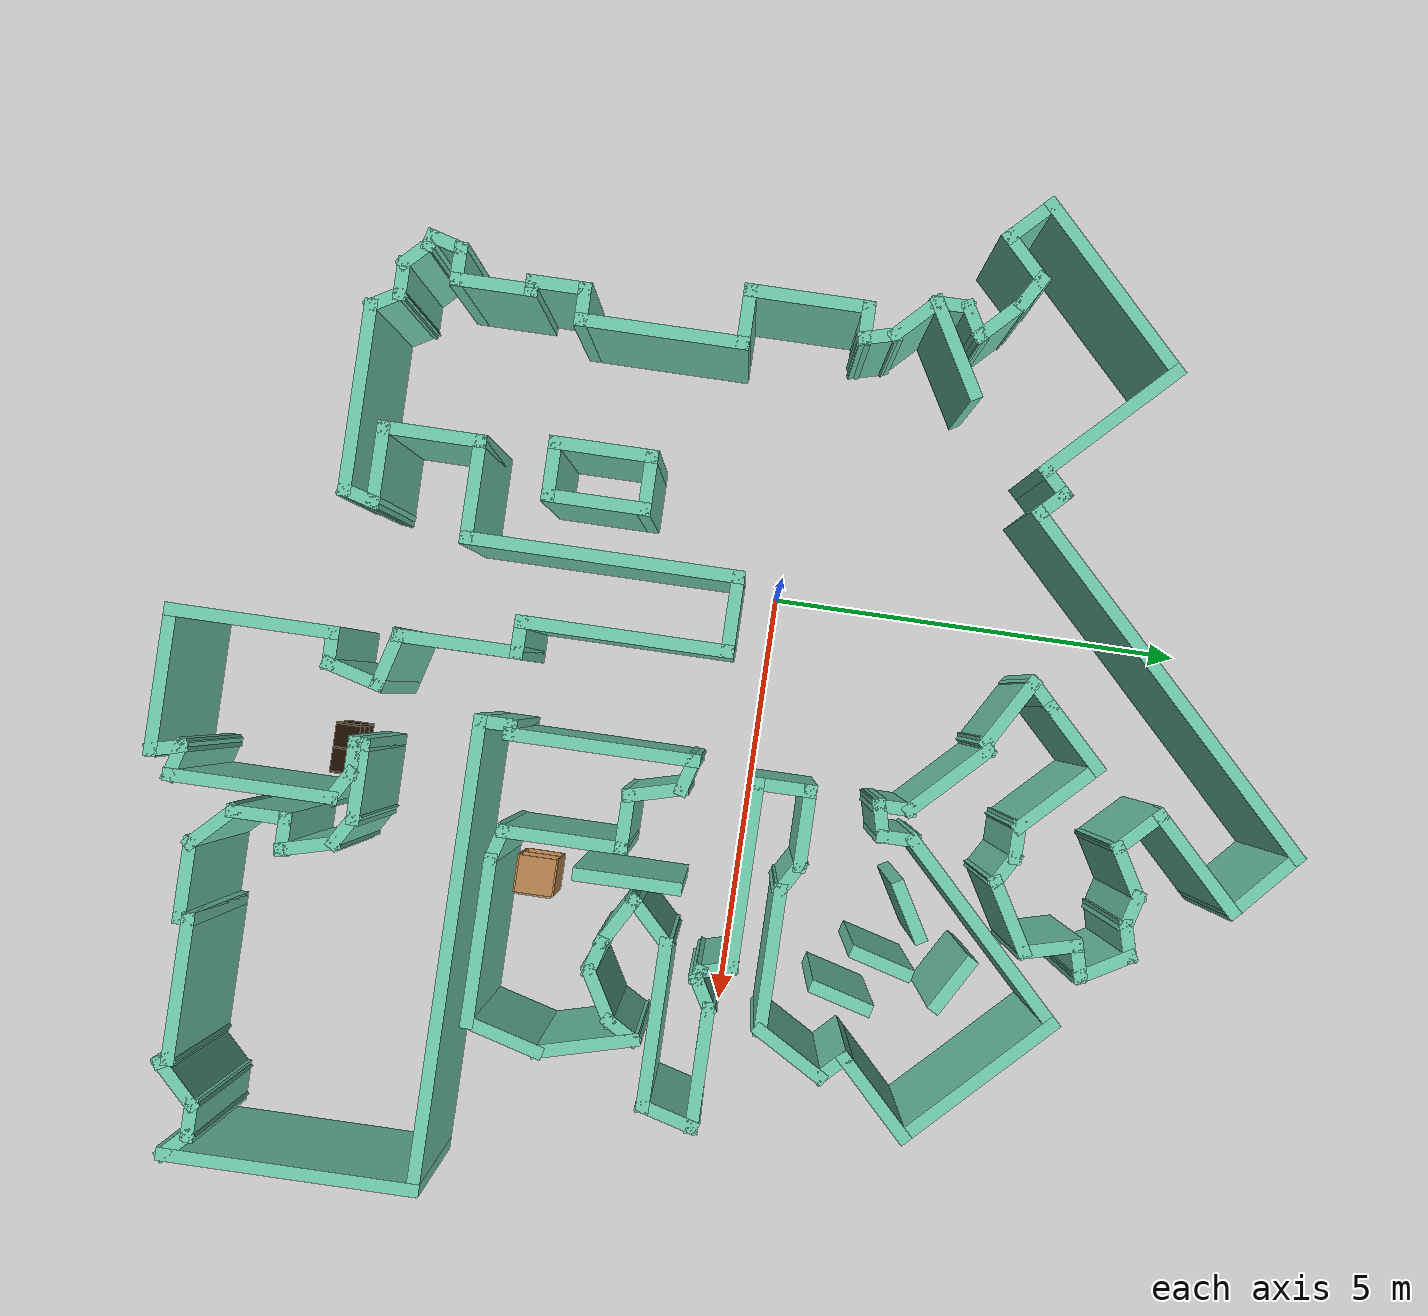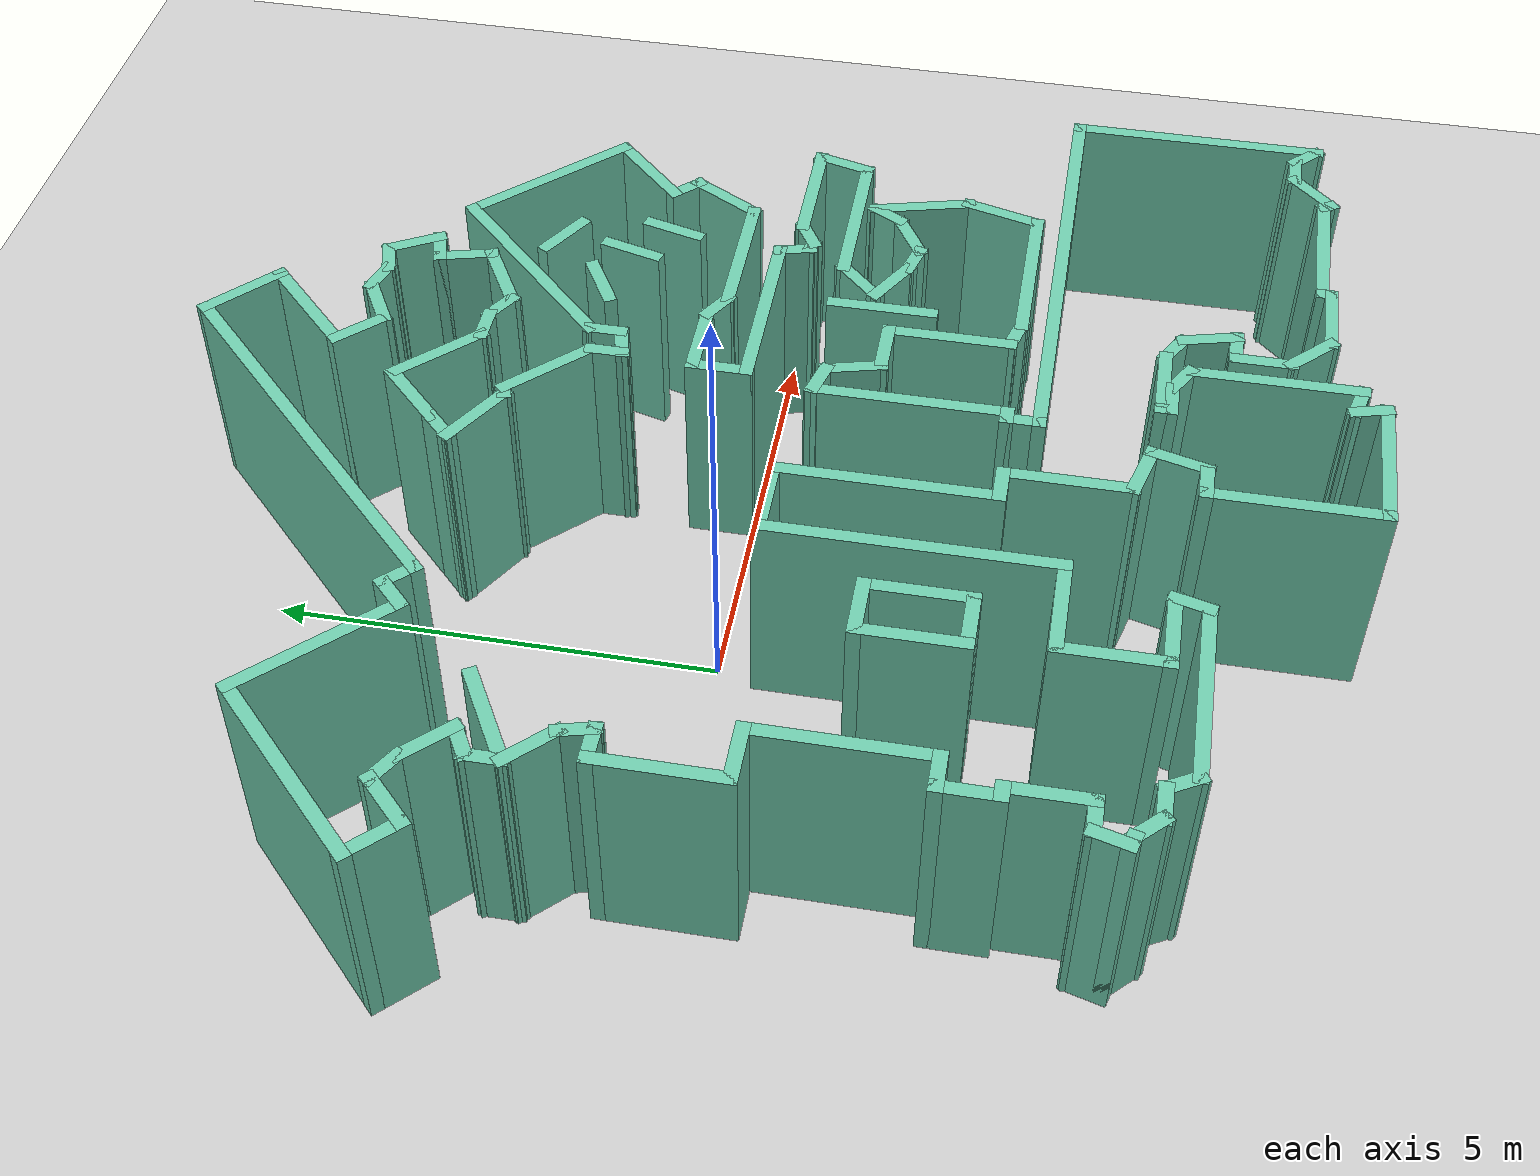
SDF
<sdf version="1.7">
 <world name="default">
  <light name="sun" type="directional">
   <pose>0 0 10 0 -0 0</pose>
   <diffuse>0.8 0.8 0.8 1</diffuse>
   <specular>0.2 0.2 0.2 1</specular>
   <attenuation>
    <range>1000</range>
    <constant>0.9</constant>
    <linear>0.01</linear>
    <quadratic>0.001</quadratic>
   </attenuation>
   <direction>-0.5 0.1 -0.9</direction>
   <spot><inner_angle>0</inner_angle><outer_angle>0</outer_angle><falloff>0</falloff></spot>
  </light>
  <model name="ground_plane">
   <static>1</static>
   <link name="link">
    <collision name="collision">
     <geometry><plane><normal>0 0 1</normal><size>100 100</size></plane></geometry>
     <surface>
      <contact><collide_bitmask>65535</collide_bitmask></contact>
      <friction><ode><mu>100</mu><mu2>50</mu2></ode></friction>
     </surface>
    </collision>
    <visual name="visual">
     <cast_shadows>0</cast_shadows>
     <geometry><plane><normal>0 0 1</normal><size>100 100</size></plane></geometry>
     <material>
      <script><uri>file://media/materials/scripts/gazebo.material</uri><name>Gazebo/Grey</name></script>
     </material>
    </visual>
   </link>
  </model>
  <gravity>0 0 -9.8</gravity>
  <magnetic_field>6e-06 2.3e-05 -4.2e-05</magnetic_field>
  <atmosphere type="adiabatic"/>
  <physics name="default_physics" default="0" type="ode">
   <max_step_size>0.001</max_step_size>
   <real_time_factor>1</real_time_factor>
   <real_time_update_rate>1000</real_time_update_rate>
  </physics>
  <scene><ambient>0.4 0.4 0.4 1</ambient><background>0.7 0.7 0.7 1</background><shadows>1</shadows></scene>
  <audio><device>default</device></audio>
  <spherical_coordinates>
   <surface_model>EARTH_WGS84</surface_model>
   <latitude_deg>0</latitude_deg>
   <longitude_deg>0</longitude_deg>
   <elevation>0</elevation>
   <heading_deg>0</heading_deg>
  </spherical_coordinates>
  <model name="map_11">
   <pose>1.26174 -0.26535 0 0 -0 0</pose>
   <link name="Wall_1">
    <collision name="Wall_1_Collision">
     <geometry><box><size>5 0.15 2.5</size></box></geometry>
     <pose>0 0 1.25 0 -0 0</pose>
    </collision>
    <visual name="Wall_1_Visual">
     <pose>0 0 1.25 0 -0 0</pose>
     <geometry><box><size>5 0.15 2.5</size></box></geometry>
     <material>
      <script><uri>file://media/materials/scripts/gazebo.material</uri><name>Gazebo/Grey</name></script>
      <ambient>0.435294 0.796078 0.67451 1</ambient>
     </material>
     <meta><layer>0</layer></meta>
    </visual>
    <pose>-0.835333 4.76863 0 0 -0 -2.35619</pose>
   </link>
   <link name="Wall_10">
    <collision name="Wall_10_Collision">
     <geometry><box><size>0.5 0.15 2.5</size></box></geometry>
     <pose>0 0 1.25 0 -0 0</pose>
    </collision>
    <visual name="Wall_10_Visual">
     <pose>0 0 1.25 0 -0 0</pose>
     <geometry><box><size>0.5 0.15 2.5</size></box></geometry>
     <material>
      <script><uri>file://media/materials/scripts/gazebo.material</uri><name>Gazebo/Grey</name></script>
      <ambient>0.435294 0.796078 0.67451 1</ambient>
     </material>
     <meta><layer>0</layer></meta>
    </visual>
    <pose>-5.01481 2.61285 0 0 -0 -0.523599</pose>
   </link>
   <link name="Wall_100">
    <collision name="Wall_100_Collision">
     <geometry><box><size>1 0.15 2.5</size></box></geometry>
     <pose>0 0 1.25 0 -0 0</pose>
    </collision>
    <visual name="Wall_100_Visual">
     <pose>0 0 1.25 0 -0 0</pose>
     <geometry><box><size>1 0.15 2.5</size></box></geometry>
     <material>
      <script><uri>file://media/materials/scripts/gazebo.material</uri><name>Gazebo/Grey</name></script>
      <ambient>0.435294 0.796078 0.67451 1</ambient>
     </material>
     <meta><layer>0</layer></meta>
    </visual>
    <pose>3.8842 1.1324 0 0 -0 1.0472</pose>
   </link>
   <link name="Wall_101">
    <collision name="Wall_101_Collision">
     <geometry><box><size>0.5 0.15 2.5</size></box></geometry>
     <pose>0 0 1.25 0 -0 0</pose>
    </collision>
    <visual name="Wall_101_Visual">
     <pose>0 0 1.25 0 -0 0</pose>
     <geometry><box><size>0.5 0.15 2.5</size></box></geometry>
     <material>
      <script><uri>file://media/materials/scripts/gazebo.material</uri><name>Gazebo/Grey</name></script>
      <ambient>0.435294 0.796078 0.67451 1</ambient>
     </material>
     <meta><layer>0</layer></meta>
    </visual>
    <pose>3.97295 1.62421 0 0 -0 2.35619</pose>
   </link>
   <link name="Wall_102">
    <collision name="Wall_102_Collision">
     <geometry><box><size>1.25 0.15 2.5</size></box></geometry>
     <pose>0 0 1.25 0 -0 0</pose>
    </collision>
    <visual name="Wall_102_Visual">
     <pose>0 0 1.25 0 -0 0</pose>
     <geometry><box><size>1.25 0.15 2.5</size></box></geometry>
     <material>
      <script><uri>file://media/materials/scripts/gazebo.material</uri><name>Gazebo/Grey</name></script>
      <ambient>0.435294 0.796078 0.67451 1</ambient>
     </material>
     <meta><layer>0</layer></meta>
    </visual>
    <pose>4.23812 2.13686 0 0 -0 0.785398</pose>
   </link>
   <link name="Wall_105">
    <collision name="Wall_105_Collision">
     <geometry><box><size>2.25 0.15 2.5</size></box></geometry>
     <pose>0 0 1.25 0 -0 0</pose>
    </collision>
    <visual name="Wall_105_Visual">
     <pose>0 0 1.25 0 -0 0</pose>
     <geometry><box><size>2.25 0.15 2.5</size></box></geometry>
     <material>
      <script><uri>file://media/materials/scripts/gazebo.material</uri><name>Gazebo/Grey</name></script>
      <ambient>0.435294 0.796078 0.67451 1</ambient>
     </material>
     <meta><layer>0</layer></meta>
    </visual>
    <pose>3.88456 3.26823 0 0 -0 2.35619</pose>
   </link>
   <link name="Wall_106">
    <collision name="Wall_106_Collision">
     <geometry><box><size>2.75 0.15 2.5</size></box></geometry>
     <pose>0 0 1.25 0 -0 0</pose>
    </collision>
    <visual name="Wall_106_Visual">
     <pose>0 0 1.25 0 -0 0</pose>
     <geometry><box><size>2.75 0.15 2.5</size></box></geometry>
     <material>
      <script><uri>file://media/materials/scripts/gazebo.material</uri><name>Gazebo/Grey</name></script>
      <ambient>0.435294 0.796078 0.67451 1</ambient>
     </material>
     <meta><layer>0</layer></meta>
    </visual>
    <pose>2.22286 3.09145 0 0 -0 -2.35619</pose>
   </link>
   <link name="Wall_107">
    <collision name="Wall_107_Collision">
     <geometry><box><size>0.5 0.15 2.5</size></box></geometry>
     <pose>0 0 1.25 0 -0 0</pose>
    </collision>
    <visual name="Wall_107_Visual">
     <pose>0 0 1.25 0 -0 0</pose>
     <geometry><box><size>0.5 0.15 2.5</size></box></geometry>
     <material>
      <script><uri>file://media/materials/scripts/gazebo.material</uri><name>Gazebo/Grey</name></script>
      <ambient>0.435294 0.796078 0.67451 1</ambient>
     </material>
     <meta><layer>0</layer></meta>
    </visual>
    <pose>1.30363 1.99721 0 0 -0 -1.5708</pose>
   </link>
   <link name="Wall_108">
    <collision name="Wall_108_Collision">
     <geometry><box><size>0.5 0.15 2.5</size></box></geometry>
     <pose>0 0 1.25 0 -0 0</pose>
    </collision>
    <visual name="Wall_108_Visual">
     <pose>0 0 1.25 0 -0 0</pose>
     <geometry><box><size>0.5 0.15 2.5</size></box></geometry>
     <material>
      <script><uri>file://media/materials/scripts/gazebo.material</uri><name>Gazebo/Grey</name></script>
      <ambient>0.435294 0.796078 0.67451 1</ambient>
     </material>
     <meta><layer>0</layer></meta>
    </visual>
    <pose>1.13459 1.77692 0 0 -0 -2.87979</pose>
   </link>
   <link name="Wall_109">
    <collision name="Wall_109_Collision">
     <geometry><box><size>0.5 0.15 2.5</size></box></geometry>
     <pose>0 0 1.25 0 -0 0</pose>
    </collision>
    <visual name="Wall_109_Visual">
     <pose>0 0 1.25 0 -0 0</pose>
     <geometry><box><size>0.5 0.15 2.5</size></box></geometry>
     <material>
      <script><uri>file://media/materials/scripts/gazebo.material</uri><name>Gazebo/Grey</name></script>
      <ambient>0.435294 0.796078 0.67451 1</ambient>
     </material>
     <meta><layer>0</layer></meta>
    </visual>
    <pose>0.965551 1.90663 0 0 -0 1.5708</pose>
   </link>
   <link name="Wall_11">
    <collision name="Wall_11_Collision">
     <geometry><box><size>0.75 0.15 2.5</size></box></geometry>
     <pose>0 0 1.25 0 -0 0</pose>
    </collision>
    <visual name="Wall_11_Visual">
     <pose>0 0 1.25 0 -0 0</pose>
     <geometry><box><size>0.75 0.15 2.5</size></box></geometry>
     <material>
      <script><uri>file://media/materials/scripts/gazebo.material</uri><name>Gazebo/Grey</name></script>
      <ambient>0.435294 0.796078 0.67451 1</ambient>
     </material>
     <meta><layer>0</layer></meta>
    </visual>
    <pose>-4.65112 2.31322 0 0 -0 -0.785398</pose>
   </link>
   <link name="Wall_110">
    <collision name="Wall_110_Collision">
     <geometry><box><size>1.25 0.15 2.5</size></box></geometry>
     <pose>0 0 1.25 0 -0 0</pose>
    </collision>
    <visual name="Wall_110_Visual">
     <pose>0 0 1.25 0 -0 0</pose>
     <geometry><box><size>1.25 0.15 2.5</size></box></geometry>
     <material>
      <script><uri>file://media/materials/scripts/gazebo.material</uri><name>Gazebo/Grey</name></script>
      <ambient>0.435294 0.796078 0.67451 1</ambient>
     </material>
     <meta><layer>0</layer></meta>
    </visual>
    <pose>0.576643 2.47054 0 0 -0 2.35619</pose>
   </link>
   <link name="Wall_111">
    <collision name="Wall_111_Collision">
     <geometry><box><size>0.25 0.15 2.5</size></box></geometry>
     <pose>0 0 1.25 0 -0 0</pose>
    </collision>
    <visual name="Wall_111_Visual">
     <pose>0 0 1.25 0 -0 0</pose>
     <geometry><box><size>0.25 0.15 2.5</size></box></geometry>
     <material>
      <script><uri>file://media/materials/scripts/gazebo.material</uri><name>Gazebo/Grey</name></script>
      <ambient>0.435294 0.796078 0.67451 1</ambient>
     </material>
     <meta><layer>0</layer></meta>
    </visual>
    <pose>0.139438 2.84651 0 0 -0 -2.87979</pose>
   </link>
   <link name="Wall_112">
    <collision name="Wall_112_Collision">
     <geometry><box><size>1 0.15 2.5</size></box></geometry>
     <pose>0 0 1.25 0 -0 0</pose>
    </collision>
    <visual name="Wall_112_Visual">
     <pose>0 0 1.25 0 -0 0</pose>
     <geometry><box><size>1 0.15 2.5</size></box></geometry>
     <material>
      <script><uri>file://media/materials/scripts/gazebo.material</uri><name>Gazebo/Grey</name></script>
      <ambient>0.435294 0.796078 0.67451 1</ambient>
     </material>
     <meta><layer>0</layer></meta>
    </visual>
    <pose>-0.276919 3.04606 0 0 -0 2.61799</pose>
   </link>
   <link name="Wall_113">
    <collision name="Wall_113_Collision">
     <geometry><box><size>0.5 0.15 2.5</size></box></geometry>
     <pose>0 0 1.25 0 -0 0</pose>
    </collision>
    <visual name="Wall_113_Visual">
     <pose>0 0 1.25 0 -0 0</pose>
     <geometry><box><size>0.5 0.15 2.5</size></box></geometry>
     <material>
      <script><uri>file://media/materials/scripts/gazebo.material</uri><name>Gazebo/Grey</name></script>
      <ambient>0.435294 0.796078 0.67451 1</ambient>
     </material>
     <meta><layer>0</layer></meta>
    </visual>
    <pose>-0.521237 3.38231 0 0 -0 0.785398</pose>
   </link>
   <link name="Wall_114">
    <collision name="Wall_114_Collision">
     <geometry><box><size>1 0.15 2.5</size></box></geometry>
     <pose>0 0 1.25 0 -0 0</pose>
    </collision>
    <visual name="Wall_114_Visual">
     <pose>0 0 1.25 0 -0 0</pose>
     <geometry><box><size>1 0.15 2.5</size></box></geometry>
     <material>
      <script><uri>file://media/materials/scripts/gazebo.material</uri><name>Gazebo/Grey</name></script>
      <ambient>0.435294 0.796078 0.67451 1</ambient>
     </material>
     <meta><layer>0</layer></meta>
    </visual>
    <pose>-0.096972 3.80657 0 0 -0 0.785398</pose>
   </link>
   <link name="Wall_115">
    <collision name="Wall_115_Collision">
     <geometry><box><size>1.25 0.15 2.5</size></box></geometry>
     <pose>0 0 1.25 0 -0 0</pose>
    </collision>
    <visual name="Wall_115_Visual">
     <pose>0 0 1.25 0 -0 0</pose>
     <geometry><box><size>1.25 0.15 2.5</size></box></geometry>
     <material>
      <script><uri>file://media/materials/scripts/gazebo.material</uri><name>Gazebo/Grey</name></script>
      <ambient>0.435294 0.796078 0.67451 1</ambient>
     </material>
     <meta><layer>0</layer></meta>
    </visual>
    <pose>0.592457 3.71818 0 0 -0 -0.785398</pose>
   </link>
   <link name="Wall_116">
    <collision name="Wall_116_Collision">
     <geometry><box><size>0.5 0.15 2.5</size></box></geometry>
     <pose>0 0 1.25 0 -0 0</pose>
    </collision>
    <visual name="Wall_116_Visual">
     <pose>0 0 1.25 0 -0 0</pose>
     <geometry><box><size>0.5 0.15 2.5</size></box></geometry>
     <material>
      <script><uri>file://media/materials/scripts/gazebo.material</uri><name>Gazebo/Grey</name></script>
      <ambient>0.435294 0.796078 0.67451 1</ambient>
     </material>
     <meta><layer>0</layer></meta>
    </visual>
    <pose>1.15637 3.32927 0 0 -0 0</pose>
   </link>
   <link name="Wall_117">
    <collision name="Wall_117_Collision">
     <geometry><box><size>0.5 0.15 2.5</size></box></geometry>
     <pose>0 0 1.25 0 -0 0</pose>
    </collision>
    <visual name="Wall_117_Visual">
     <pose>0 0 1.25 0 -0 0</pose>
     <geometry><box><size>0.5 0.15 2.5</size></box></geometry>
     <material>
      <script><uri>file://media/materials/scripts/gazebo.material</uri><name>Gazebo/Grey</name></script>
      <ambient>0.435294 0.796078 0.67451 1</ambient>
     </material>
     <meta><layer>0</layer></meta>
    </visual>
    <pose>1.48292 3.24178 0 0 -0 -0.523599</pose>
   </link>
   <link name="Wall_118">
    <collision name="Wall_118_Collision">
     <geometry><box><size>1 0.15 2.5</size></box></geometry>
     <pose>0 0 1.25 0 -0 0</pose>
    </collision>
    <visual name="Wall_118_Visual">
     <pose>0 0 1.25 0 -0 0</pose>
     <geometry><box><size>1 0.15 2.5</size></box></geometry>
     <material>
      <script><uri>file://media/materials/scripts/gazebo.material</uri><name>Gazebo/Grey</name></script>
      <ambient>0.435294 0.796078 0.67451 1</ambient>
     </material>
     <meta><layer>0</layer></meta>
    </visual>
    <pose>2.00253 3.36678 0 0 -0 0.523599</pose>
   </link>
   <link name="Wall_119">
    <collision name="Wall_119_Collision">
     <geometry><box><size>0.75 0.15 2.5</size></box></geometry>
     <pose>0 0 1.25 0 -0 0</pose>
    </collision>
    <visual name="Wall_119_Visual">
     <pose>0 0 1.25 0 -0 0</pose>
     <geometry><box><size>0.75 0.15 2.5</size></box></geometry>
     <material>
      <script><uri>file://media/materials/scripts/gazebo.material</uri><name>Gazebo/Grey</name></script>
      <ambient>0.435294 0.796078 0.67451 1</ambient>
     </material>
     <meta><layer>0</layer></meta>
    </visual>
    <pose>2.29295 3.86905 0 0 -0 1.8326</pose>
   </link>
   <link name="Wall_12">
    <collision name="Wall_12_Collision">
     <geometry><box><size>0.5 0.15 2.5</size></box></geometry>
     <pose>0 0 1.25 0 -0 0</pose>
    </collision>
    <visual name="Wall_12_Visual">
     <pose>0 0 1.25 0 -0 0</pose>
     <geometry><box><size>0.5 0.15 2.5</size></box></geometry>
     <material>
      <script><uri>file://media/materials/scripts/gazebo.material</uri><name>Gazebo/Grey</name></script>
      <ambient>0.435294 0.796078 0.67451 1</ambient>
     </material>
     <meta><layer>0</layer></meta>
    </visual>
    <pose>-4.59054 2.01358 0 0 -0 -2.61799</pose>
   </link>
   <link name="Wall_120">
    <collision name="Wall_120_Collision">
     <geometry><box><size>0.5 0.15 2.5</size></box></geometry>
     <pose>0 0 1.25 0 -0 0</pose>
    </collision>
    <visual name="Wall_120_Visual">
     <pose>0 0 1.25 0 -0 0</pose>
     <geometry><box><size>0.5 0.15 2.5</size></box></geometry>
     <material>
      <script><uri>file://media/materials/scripts/gazebo.material</uri><name>Gazebo/Grey</name></script>
      <ambient>0.435294 0.796078 0.67451 1</ambient>
     </material>
     <meta><layer>0</layer></meta>
    </visual>
    <pose>2.38434 4.20412 0 0 -0 0.261799</pose>
   </link>
   <link name="Wall_121">
    <collision name="Wall_121_Collision">
     <geometry><box><size>0.75 0.15 2.5</size></box></geometry>
     <pose>0 0 1.25 0 -0 0</pose>
    </collision>
    <visual name="Wall_121_Visual">
     <pose>0 0 1.25 0 -0 0</pose>
     <geometry><box><size>0.75 0.15 2.5</size></box></geometry>
     <material>
      <script><uri>file://media/materials/scripts/gazebo.material</uri><name>Gazebo/Grey</name></script>
      <ambient>0.435294 0.796078 0.67451 1</ambient>
     </material>
     <meta><layer>0</layer></meta>
    </visual>
    <pose>2.40338 4.50922 0 0 -0 2.0944</pose>
   </link>
   <link name="Wall_122">
    <collision name="Wall_122_Collision">
     <geometry><box><size>0.5 0.15 2.5</size></box></geometry>
     <pose>0 0 1.25 0 -0 0</pose>
    </collision>
    <visual name="Wall_122_Visual">
     <pose>0 0 1.25 0 -0 0</pose>
     <geometry><box><size>0.5 0.15 2.5</size></box></geometry>
     <material>
      <script><uri>file://media/materials/scripts/gazebo.material</uri><name>Gazebo/Grey</name></script>
      <ambient>0.435294 0.796078 0.67451 1</ambient>
     </material>
     <meta><layer>0</layer></meta>
    </visual>
    <pose>2.08434 4.72374 0 0 -0 -2.87979</pose>
   </link>
   <link name="Wall_123">
    <collision name="Wall_123_Collision">
     <geometry><box><size>0.5 0.15 2.5</size></box></geometry>
     <pose>0 0 1.25 0 -0 0</pose>
    </collision>
    <visual name="Wall_123_Visual">
     <pose>0 0 1.25 0 -0 0</pose>
     <geometry><box><size>0.5 0.15 2.5</size></box></geometry>
     <material>
      <script><uri>file://media/materials/scripts/gazebo.material</uri><name>Gazebo/Grey</name></script>
      <ambient>0.435294 0.796078 0.67451 1</ambient>
     </material>
     <meta><layer>0</layer></meta>
    </visual>
    <pose>1.74627 4.72374 0 0 -0 2.87979</pose>
   </link>
   <link name="Wall_124">
    <collision name="Wall_124_Collision">
     <geometry><box><size>0.75 0.15 2.5</size></box></geometry>
     <pose>0 0 1.25 0 -0 0</pose>
    </collision>
    <visual name="Wall_124_Visual">
     <pose>0 0 1.25 0 -0 0</pose>
     <geometry><box><size>0.75 0.15 2.5</size></box></geometry>
     <material>
      <script><uri>file://media/materials/scripts/gazebo.material</uri><name>Gazebo/Grey</name></script>
      <ambient>0.435294 0.796078 0.67451 1</ambient>
     </material>
     <meta><layer>0</layer></meta>
    </visual>
    <pose>1.31742 4.61903 0 0 -0 -2.61799</pose>
   </link>
   <link name="Wall_125">
    <collision name="Wall_125_Collision">
     <geometry><box><size>0.75 0.15 2.5</size></box></geometry>
     <pose>0 0 1.25 0 -0 0</pose>
    </collision>
    <visual name="Wall_125_Visual">
     <pose>0 0 1.25 0 -0 0</pose>
     <geometry><box><size>0.75 0.15 2.5</size></box></geometry>
     <material>
      <script><uri>file://media/materials/scripts/gazebo.material</uri><name>Gazebo/Grey</name></script>
      <ambient>0.435294 0.796078 0.67451 1</ambient>
     </material>
     <meta><layer>0</layer></meta>
    </visual>
    <pose>0.845483 4.68116 0 0 -0 2.35619</pose>
   </link>
   <link name="Wall_126">
    <collision name="Wall_126_Collision">
     <geometry><box><size>1.5 0.15 2.5</size></box></geometry>
     <pose>0 0 1.25 0 -0 0</pose>
    </collision>
    <visual name="Wall_126_Visual">
     <pose>0 0 1.25 0 -0 0</pose>
     <geometry><box><size>1.5 0.15 2.5</size></box></geometry>
     <material>
      <script><uri>file://media/materials/scripts/gazebo.material</uri><name>Gazebo/Grey</name></script>
      <ambient>0.435294 0.796078 0.67451 1</ambient>
     </material>
     <meta><layer>0</layer></meta>
    </visual>
    <pose>1.11065 5.37059 0 0 -0 0.785398</pose>
   </link>
   <link name="Wall_129">
    <collision name="Wall_129_Collision">
     <geometry><box><size>1.10177 0.15 2.5</size></box></geometry>
     <pose>0 0 1.25 0 -0 0</pose>
    </collision>
    <visual name="Wall_129_Visual">
     <pose>0 0 1.25 0 -0 0</pose>
     <geometry><box><size>1.10177 0.15 2.5</size></box></geometry>
     <material>
      <script><uri>file://media/materials/scripts/gazebo.material</uri><name>Gazebo/Grey</name></script>
      <ambient>0.435294 0.796078 0.67451 1</ambient>
     </material>
     <meta><layer>0</layer></meta>
    </visual>
    <pose>1.23367 6.16563 0 0 -0 2.41051</pose>
   </link>
   <link name="Wall_13">
    <collision name="Wall_13_Collision">
     <geometry><box><size>0.5 0.15 2.5</size></box></geometry>
     <pose>0 0 1.25 0 -0 0</pose>
    </collision>
    <visual name="Wall_13_Visual">
     <pose>0 0 1.25 0 -0 0</pose>
     <geometry><box><size>0.5 0.15 2.5</size></box></geometry>
     <material>
      <script><uri>file://media/materials/scripts/gazebo.material</uri><name>Gazebo/Grey</name></script>
      <ambient>0.435294 0.796078 0.67451 1</ambient>
     </material>
     <meta><layer>0</layer></meta>
    </visual>
    <pose>-4.7421 1.75108 0 0 -0 -1.5708</pose>
   </link>
   <link name="Wall_131">
    <collision name="Wall_131_Collision">
     <geometry><box><size>1.25 0.15 2.5</size></box></geometry>
     <pose>0 0 1.25 0 -0 0</pose>
    </collision>
    <visual name="Wall_131_Visual">
     <pose>0 0 1.25 0 -0 0</pose>
     <geometry><box><size>1.25 0.15 2.5</size></box></geometry>
     <material>
      <script><uri>file://media/materials/scripts/gazebo.material</uri><name>Gazebo/Grey</name></script>
      <ambient>0.435294 0.796078 0.67451 1</ambient>
     </material>
     <meta><layer>0</layer></meta>
    </visual>
    <pose>-4.26578 1.85108 0 0 -0 0.523599</pose>
   </link>
   <link name="Wall_133">
    <collision name="Wall_133_Collision">
     <geometry><box><size>1.25 0.15 2.5</size></box></geometry>
     <pose>0 0 1.25 0 -0 0</pose>
    </collision>
    <visual name="Wall_133_Visual">
     <pose>0 0 1.25 0 -0 0</pose>
     <geometry><box><size>1.25 0.15 2.5</size></box></geometry>
     <material>
      <script><uri>file://media/materials/scripts/gazebo.material</uri><name>Gazebo/Grey</name></script>
      <ambient>0.435294 0.796078 0.67451 1</ambient>
     </material>
     <meta><layer>0</layer></meta>
    </visual>
    <pose>2.22342 -0.962039 0 0 -0 -1.5708</pose>
   </link>
   <link name="Wall_135">
    <collision name="Wall_135_Collision">
     <geometry><box><size>1.25 0.15 2.5</size></box></geometry>
     <pose>0 0 1.25 0 -0 0</pose>
    </collision>
    <visual name="Wall_135_Visual">
     <pose>0 0 1.25 0 -0 0</pose>
     <geometry><box><size>1.25 0.15 2.5</size></box></geometry>
     <material>
      <script><uri>file://media/materials/scripts/gazebo.material</uri><name>Gazebo/Grey</name></script>
      <ambient>0.435294 0.796078 0.67451 1</ambient>
     </material>
     <meta><layer>0</layer></meta>
    </visual>
    <pose>-2.56461 -1.91965 0 0 -0 -1.5708</pose>
   </link>
   <link name="Wall_136">
    <collision name="Wall_136_Collision">
     <geometry><box><size>0.75 0.15 2.5</size></box></geometry>
     <pose>0 0 1.25 0 -0 0</pose>
    </collision>
    <visual name="Wall_136_Visual">
     <pose>0 0 1.25 0 -0 0</pose>
     <geometry><box><size>0.75 0.15 2.5</size></box></geometry>
     <material>
      <script><uri>file://media/materials/scripts/gazebo.material</uri><name>Gazebo/Grey</name></script>
      <ambient>0.435294 0.796078 0.67451 1</ambient>
     </material>
     <meta><layer>0</layer></meta>
    </visual>
    <pose>-2.26461 -2.46965 0 0 -0 0</pose>
   </link>
   <link name="Wall_137">
    <collision name="Wall_137_Collision">
     <geometry><box><size>1.25 0.15 2.5</size></box></geometry>
     <pose>0 0 1.25 0 -0 0</pose>
    </collision>
    <visual name="Wall_137_Visual">
     <pose>0 0 1.25 0 -0 0</pose>
     <geometry><box><size>1.25 0.15 2.5</size></box></geometry>
     <material>
      <script><uri>file://media/materials/scripts/gazebo.material</uri><name>Gazebo/Grey</name></script>
      <ambient>0.435294 0.796078 0.67451 1</ambient>
     </material>
     <meta><layer>0</layer></meta>
    </visual>
    <pose>-1.96461 -1.91965 0 0 -0 1.5708</pose>
   </link>
   <link name="Wall_138">
    <collision name="Wall_138_Collision">
     <geometry><box><size>0.75 0.15 2.5</size></box></geometry>
     <pose>0 0 1.25 0 -0 0</pose>
    </collision>
    <visual name="Wall_138_Visual">
     <pose>0 0 1.25 0 -0 0</pose>
     <geometry><box><size>0.75 0.15 2.5</size></box></geometry>
     <material>
      <script><uri>file://media/materials/scripts/gazebo.material</uri><name>Gazebo/Grey</name></script>
      <ambient>0.435294 0.796078 0.67451 1</ambient>
     </material>
     <meta><layer>0</layer></meta>
    </visual>
    <pose>-2.26461 -1.36965 0 0 -0 -3.14159</pose>
   </link>
   <link name="Wall_14">
    <collision name="Wall_14_Collision">
     <geometry><box><size>0.75 0.15 2.5</size></box></geometry>
     <pose>0 0 1.25 0 -0 0</pose>
    </collision>
    <visual name="Wall_14_Visual">
     <pose>0 0 1.25 0 -0 0</pose>
     <geometry><box><size>0.75 0.15 2.5</size></box></geometry>
     <material>
      <script><uri>file://media/materials/scripts/gazebo.material</uri><name>Gazebo/Grey</name></script>
      <ambient>0.435294 0.796078 0.67451 1</ambient>
     </material>
     <meta><layer>0</layer></meta>
    </visual>
    <pose>-4.52997 1.36395 0 0 -0 -0.785398</pose>
   </link>
   <link name="Wall_140">
    <collision name="Wall_140_Collision">
     <geometry><box><size>0.75 0.15 2.5</size></box></geometry>
     <pose>0 0 1.25 0 -0 0</pose>
    </collision>
    <visual name="Wall_140_Visual">
     <pose>0 0 1.25 0 -0 0</pose>
     <geometry><box><size>0.75 0.15 2.5</size></box></geometry>
     <material>
      <script><uri>file://media/materials/scripts/gazebo.material</uri><name>Gazebo/Grey</name></script>
      <ambient>0.435294 0.796078 0.67451 1</ambient>
     </material>
     <meta><layer>0</layer></meta>
    </visual>
    <pose>2.85563 2.84279 0 0 -0 -0.523599</pose>
   </link>
   <link name="Wall_142">
    <collision name="Wall_142_Collision">
     <geometry><box><size>0.75 0.15 2.5</size></box></geometry>
     <pose>0 0 1.25 0 -0 0</pose>
    </collision>
    <visual name="Wall_142_Visual">
     <pose>0 0 1.25 0 -0 0</pose>
     <geometry><box><size>0.75 0.15 2.5</size></box></geometry>
     <material>
      <script><uri>file://media/materials/scripts/gazebo.material</uri><name>Gazebo/Grey</name></script>
      <ambient>0.435294 0.796078 0.67451 1</ambient>
     </material>
     <meta><layer>0</layer></meta>
    </visual>
    <pose>3.18319 1.6124 0 0 -0 -1.8326</pose>
   </link>
   <link name="Wall_144">
    <collision name="Wall_144_Collision">
     <geometry><box><size>0.75 0.15 2.5</size></box></geometry>
     <pose>0 0 1.25 0 -0 0</pose>
    </collision>
    <visual name="Wall_144_Visual">
     <pose>0 0 1.25 0 -0 0</pose>
     <geometry><box><size>0.75 0.15 2.5</size></box></geometry>
     <material>
      <script><uri>file://media/materials/scripts/gazebo.material</uri><name>Gazebo/Grey</name></script>
      <ambient>0.435294 0.796078 0.67451 1</ambient>
     </material>
     <meta><layer>0</layer></meta>
    </visual>
    <pose>2.11083 2.23838 0 0 -0 0.523599</pose>
   </link>
   <link name="Wall_146">
    <collision name="Wall_146_Collision">
     <geometry><box><size>0.75 0.15 2.5</size></box></geometry>
     <pose>0 0 1.25 0 -0 0</pose>
    </collision>
    <visual name="Wall_146_Visual">
     <pose>0 0 1.25 0 -0 0</pose>
     <geometry><box><size>0.75 0.15 2.5</size></box></geometry>
     <material>
      <script><uri>file://media/materials/scripts/gazebo.material</uri><name>Gazebo/Grey</name></script>
      <ambient>0.435294 0.796078 0.67451 1</ambient>
     </material>
     <meta><layer>0</layer></meta>
    </visual>
    <pose>2.73098 2.0114 0 0 -0 -1.8326</pose>
   </link>
   <link name="Wall_15">
    <collision name="Wall_15_Collision">
     <geometry><box><size>0.5 0.15 2.5</size></box></geometry>
     <pose>0 0 1.25 0 -0 0</pose>
    </collision>
    <visual name="Wall_15_Visual">
     <pose>0 0 1.25 0 -0 0</pose>
     <geometry><box><size>0.5 0.15 2.5</size></box></geometry>
     <material>
      <script><uri>file://media/materials/scripts/gazebo.material</uri><name>Gazebo/Grey</name></script>
      <ambient>0.435294 0.796078 0.67451 1</ambient>
     </material>
     <meta><layer>0</layer></meta>
    </visual>
    <pose>-4.27254 0.982783 0 0 -0 -1.309</pose>
   </link>
   <link name="Wall_16">
    <collision name="Wall_16_Collision">
     <geometry><box><size>0.5 0.15 2.5</size></box></geometry>
     <pose>0 0 1.25 0 -0 0</pose>
    </collision>
    <visual name="Wall_16_Visual">
     <pose>0 0 1.25 0 -0 0</pose>
     <geometry><box><size>0.5 0.15 2.5</size></box></geometry>
     <material>
      <script><uri>file://media/materials/scripts/gazebo.material</uri><name>Gazebo/Grey</name></script>
      <ambient>0.435294 0.796078 0.67451 1</ambient>
     </material>
     <meta><layer>0</layer></meta>
    </visual>
    <pose>-4.40225 0.813746 0 0 -0 3.14159</pose>
   </link>
   <link name="Wall_17">
    <collision name="Wall_17_Collision">
     <geometry><box><size>1.5 0.15 2.5</size></box></geometry>
     <pose>0 0 1.25 0 -0 0</pose>
    </collision>
    <visual name="Wall_17_Visual">
     <pose>0 0 1.25 0 -0 0</pose>
     <geometry><box><size>1.5 0.15 2.5</size></box></geometry>
     <material>
      <script><uri>file://media/materials/scripts/gazebo.material</uri><name>Gazebo/Grey</name></script>
      <ambient>0.435294 0.796078 0.67451 1</ambient>
     </material>
     <meta><layer>0</layer></meta>
    </visual>
    <pose>-4.57725 0.138746 0 0 -0 -1.5708</pose>
   </link>
   <link name="Wall_18">
    <collision name="Wall_18_Collision">
     <geometry><box><size>0.75 0.15 2.5</size></box></geometry>
     <pose>0 0 1.25 0 -0 0</pose>
    </collision>
    <visual name="Wall_18_Visual">
     <pose>0 0 1.25 0 -0 0</pose>
     <geometry><box><size>0.75 0.15 2.5</size></box></geometry>
     <material>
      <script><uri>file://media/materials/scripts/gazebo.material</uri><name>Gazebo/Grey</name></script>
      <ambient>0.435294 0.796078 0.67451 1</ambient>
     </material>
     <meta><layer>0</layer></meta>
    </visual>
    <pose>-4.27725 -0.536255 0 0 -0 0</pose>
   </link>
   <link name="Wall_19">
    <collision name="Wall_19_Collision">
     <geometry><box><size>2 0.15 2.5</size></box></geometry>
     <pose>0 0 1.25 0 -0 0</pose>
    </collision>
    <visual name="Wall_19_Visual">
     <pose>0 0 1.25 0 -0 0</pose>
     <geometry><box><size>2 0.15 2.5</size></box></geometry>
     <material>
      <script><uri>file://media/materials/scripts/gazebo.material</uri><name>Gazebo/Grey</name></script>
      <ambient>0.435294 0.796078 0.67451 1</ambient>
     </material>
     <meta><layer>0</layer></meta>
    </visual>
    <pose>-3.97725 -1.46125 0 0 -0 -1.5708</pose>
   </link>
   <link name="Wall_2">
    <collision name="Wall_2_Collision">
     <geometry><box><size>0.5 0.15 2.5</size></box></geometry>
     <pose>0 0 1.25 0 -0 0</pose>
    </collision>
    <visual name="Wall_2_Visual">
     <pose>0 0 1.25 0 -0 0</pose>
     <geometry><box><size>0.5 0.15 2.5</size></box></geometry>
     <material>
      <script><uri>file://media/materials/scripts/gazebo.material</uri><name>Gazebo/Grey</name></script>
      <ambient>0.435294 0.796078 0.67451 1</ambient>
     </material>
     <meta><layer>0</layer></meta>
    </visual>
    <pose>-2.67381 3.17765 0 0 -0 2.35619</pose>
   </link>
   <link name="Wall_20">
    <collision name="Wall_20_Collision">
     <geometry><box><size>0.5 0.15 2.5</size></box></geometry>
     <pose>0 0 1.25 0 -0 0</pose>
    </collision>
    <visual name="Wall_20_Visual">
     <pose>0 0 1.25 0 -0 0</pose>
     <geometry><box><size>0.5 0.15 2.5</size></box></geometry>
     <material>
      <script><uri>file://media/materials/scripts/gazebo.material</uri><name>Gazebo/Grey</name></script>
      <ambient>0.435294 0.796078 0.67451 1</ambient>
     </material>
     <meta><layer>0</layer></meta>
    </visual>
    <pose>-4.15225 -2.38625 0 0 -0 3.14159</pose>
   </link>
   <link name="Wall_21">
    <collision name="Wall_21_Collision">
     <geometry><box><size>0.75 0.15 2.5</size></box></geometry>
     <pose>0 0 1.25 0 -0 0</pose>
    </collision>
    <visual name="Wall_21_Visual">
     <pose>0 0 1.25 0 -0 0</pose>
     <geometry><box><size>0.75 0.15 2.5</size></box></geometry>
     <material>
      <script><uri>file://media/materials/scripts/gazebo.material</uri><name>Gazebo/Grey</name></script>
      <ambient>0.435294 0.796078 0.67451 1</ambient>
     </material>
     <meta><layer>0</layer></meta>
    </visual>
    <pose>-4.32725 -2.68626 0 0 -0 -1.5708</pose>
   </link>
   <link name="Wall_24">
    <collision name="Wall_24_Collision">
     <geometry><box><size>0.25 0.15 2.5</size></box></geometry>
     <pose>0 0 1.25 0 -0 0</pose>
    </collision>
    <visual name="Wall_24_Visual">
     <pose>0 0 1.25 0 -0 0</pose>
     <geometry><box><size>0.25 0.15 2.5</size></box></geometry>
     <material>
      <script><uri>file://media/materials/scripts/gazebo.material</uri><name>Gazebo/Grey</name></script>
      <ambient>0.435294 0.796078 0.67451 1</ambient>
     </material>
     <meta><layer>0</layer></meta>
    </visual>
    <pose>-4.27725 -2.98625 0 0 -0 0</pose>
   </link>
   <link name="Wall_25">
    <collision name="Wall_25_Collision">
     <geometry><box><size>1 0.15 2.5</size></box></geometry>
     <pose>0 0 1.25 0 -0 0</pose>
    </collision>
    <visual name="Wall_25_Visual">
     <pose>0 0 1.25 0 -0 0</pose>
     <geometry><box><size>1 0.15 2.5</size></box></geometry>
     <material>
      <script><uri>file://media/materials/scripts/gazebo.material</uri><name>Gazebo/Grey</name></script>
      <ambient>0.435294 0.796078 0.67451 1</ambient>
     </material>
     <meta><layer>0</layer></meta>
    </visual>
    <pose>-4.22725 -3.41125 0 0 -0 -1.5708</pose>
   </link>
   <link name="Wall_26">
    <collision name="Wall_26_Collision">
     <geometry><box><size>0.5 0.15 2.5</size></box></geometry>
     <pose>0 0 1.25 0 -0 0</pose>
    </collision>
    <visual name="Wall_26_Visual">
     <pose>0 0 1.25 0 -0 0</pose>
     <geometry><box><size>0.5 0.15 2.5</size></box></geometry>
     <material>
      <script><uri>file://media/materials/scripts/gazebo.material</uri><name>Gazebo/Grey</name></script>
      <ambient>0.435294 0.796078 0.67451 1</ambient>
     </material>
     <meta><layer>0</layer></meta>
    </visual>
    <pose>-4.40225 -3.83625 0 0 -0 3.14159</pose>
   </link>
   <link name="Wall_27">
    <collision name="Wall_27_Collision">
     <geometry><box><size>0.5 0.15 2.5</size></box></geometry>
     <pose>0 0 1.25 0 -0 0</pose>
    </collision>
    <visual name="Wall_27_Visual">
     <pose>0 0 1.25 0 -0 0</pose>
     <geometry><box><size>0.5 0.15 2.5</size></box></geometry>
     <material>
      <script><uri>file://media/materials/scripts/gazebo.material</uri><name>Gazebo/Grey</name></script>
      <ambient>0.435294 0.796078 0.67451 1</ambient>
     </material>
     <meta><layer>0</layer></meta>
    </visual>
    <pose>-4.62254 -4.00529 0 0 -0 -1.8326</pose>
   </link>
   <link name="Wall_28">
    <collision name="Wall_28_Collision">
     <geometry><box><size>0.25 0.15 2.5</size></box></geometry>
     <pose>0 0 1.25 0 -0 0</pose>
    </collision>
    <visual name="Wall_28_Visual">
     <pose>0 0 1.25 0 -0 0</pose>
     <geometry><box><size>0.25 0.15 2.5</size></box></geometry>
     <material>
      <script><uri>file://media/materials/scripts/gazebo.material</uri><name>Gazebo/Grey</name></script>
      <ambient>0.435294 0.796078 0.67451 1</ambient>
     </material>
     <meta><layer>0</layer></meta>
    </visual>
    <pose>-4.61954 -4.18727 0 0 -0 -0.261799</pose>
   </link>
   <link name="Wall_29">
    <collision name="Wall_29_Collision">
     <geometry><box><size>0.5 0.15 2.5</size></box></geometry>
     <pose>0 0 1.25 0 -0 0</pose>
    </collision>
    <visual name="Wall_29_Visual">
     <pose>0 0 1.25 0 -0 0</pose>
     <geometry><box><size>0.5 0.15 2.5</size></box></geometry>
     <material>
      <script><uri>file://media/materials/scripts/gazebo.material</uri><name>Gazebo/Grey</name></script>
      <ambient>0.435294 0.796078 0.67451 1</ambient>
     </material>
     <meta><layer>0</layer></meta>
    </visual>
    <pose>-4.4475 -4.32395 0 0 -0 -0.785398</pose>
   </link>
   <link name="Wall_3">
    <collision name="Wall_3_Collision">
     <geometry><box><size>0.5 0.15 2.5</size></box></geometry>
     <pose>0 0 1.25 0 -0 0</pose>
    </collision>
    <visual name="Wall_3_Visual">
     <pose>0 0 1.25 0 -0 0</pose>
     <geometry><box><size>0.5 0.15 2.5</size></box></geometry>
     <material>
      <script><uri>file://media/materials/scripts/gazebo.material</uri><name>Gazebo/Grey</name></script>
      <ambient>0.435294 0.796078 0.67451 1</ambient>
     </material>
     <meta><layer>0</layer></meta>
    </visual>
    <pose>-2.9213 3.17765 0 0 -0 -2.35619</pose>
   </link>
   <link name="Wall_30">
    <collision name="Wall_30_Collision">
     <geometry><box><size>0.5 0.15 2.5</size></box></geometry>
     <pose>0 0 1.25 0 -0 0</pose>
    </collision>
    <visual name="Wall_30_Visual">
     <pose>0 0 1.25 0 -0 0</pose>
     <geometry><box><size>0.5 0.15 2.5</size></box></geometry>
     <material>
      <script><uri>file://media/materials/scripts/gazebo.material</uri><name>Gazebo/Grey</name></script>
      <ambient>0.435294 0.796078 0.67451 1</ambient>
     </material>
     <meta><layer>0</layer></meta>
    </visual>
    <pose>-4.14875 -4.4477 0 0 -0 0</pose>
   </link>
   <link name="Wall_31">
    <collision name="Wall_31_Collision">
     <geometry><box><size>0.5 0.15 2.5</size></box></geometry>
     <pose>0 0 1.25 0 -0 0</pose>
    </collision>
    <visual name="Wall_31_Visual">
     <pose>0 0 1.25 0 -0 0</pose>
     <geometry><box><size>0.5 0.15 2.5</size></box></geometry>
     <material>
      <script><uri>file://media/materials/scripts/gazebo.material</uri><name>Gazebo/Grey</name></script>
      <ambient>0.435294 0.796078 0.67451 1</ambient>
     </material>
     <meta><layer>0</layer></meta>
    </visual>
    <pose>-3.88625 -4.59925 0 0 -0 -1.0472</pose>
   </link>
   <link name="Wall_32">
    <collision name="Wall_32_Collision">
     <geometry><box><size>2.25 0.15 2.5</size></box></geometry>
     <pose>0 0 1.25 0 -0 0</pose>
    </collision>
    <visual name="Wall_32_Visual">
     <pose>0 0 1.25 0 -0 0</pose>
     <geometry><box><size>2.25 0.15 2.5</size></box></geometry>
     <material>
      <script><uri>file://media/materials/scripts/gazebo.material</uri><name>Gazebo/Grey</name></script>
      <ambient>0.435294 0.796078 0.67451 1</ambient>
     </material>
     <meta><layer>0</layer></meta>
    </visual>
    <pose>-2.74875 -4.75081 0 0 -0 0</pose>
   </link>
   <link name="Wall_33">
    <collision name="Wall_33_Collision">
     <geometry><box><size>0.5 0.15 2.5</size></box></geometry>
     <pose>0 0 1.25 0 -0 0</pose>
    </collision>
    <visual name="Wall_33_Visual">
     <pose>0 0 1.25 0 -0 0</pose>
     <geometry><box><size>0.5 0.15 2.5</size></box></geometry>
     <material>
      <script><uri>file://media/materials/scripts/gazebo.material</uri><name>Gazebo/Grey</name></script>
      <ambient>0.435294 0.796078 0.67451 1</ambient>
     </material>
     <meta><layer>0</layer></meta>
    </visual>
    <pose>-1.65346 -4.58177 0 0 -0 1.309</pose>
   </link>
   <link name="Wall_34">
    <collision name="Wall_34_Collision">
     <geometry><box><size>1 0.15 2.5</size></box></geometry>
     <pose>0 0 1.25 0 -0 0</pose>
    </collision>
    <visual name="Wall_34_Visual">
     <pose>0 0 1.25 0 -0 0</pose>
     <geometry><box><size>1 0.15 2.5</size></box></geometry>
     <material>
      <script><uri>file://media/materials/scripts/gazebo.material</uri><name>Gazebo/Grey</name></script>
      <ambient>0.435294 0.796078 0.67451 1</ambient>
     </material>
     <meta><layer>0</layer></meta>
    </visual>
    <pose>-2.03317 -4.41273 0 0 -0 3.14159</pose>
   </link>
   <link name="Wall_35">
    <collision name="Wall_35_Collision">
     <geometry><box><size>1.25 0.15 2.5</size></box></geometry>
     <pose>0 0 1.25 0 -0 0</pose>
    </collision>
    <visual name="Wall_35_Visual">
     <pose>0 0 1.25 0 -0 0</pose>
     <geometry><box><size>1.25 0.15 2.5</size></box></geometry>
     <material>
      <script><uri>file://media/materials/scripts/gazebo.material</uri><name>Gazebo/Grey</name></script>
      <ambient>0.435294 0.796078 0.67451 1</ambient>
     </material>
     <meta><layer>0</layer></meta>
    </visual>
    <pose>-2.45817 -3.86273 0 0 -0 1.5708</pose>
   </link>
   <link name="Wall_36">
    <collision name="Wall_36_Collision">
     <geometry><box><size>1.25 0.15 2.5</size></box></geometry>
     <pose>0 0 1.25 0 -0 0</pose>
    </collision>
    <visual name="Wall_36_Visual">
     <pose>0 0 1.25 0 -0 0</pose>
     <geometry><box><size>1.25 0.15 2.5</size></box></geometry>
     <material>
      <script><uri>file://media/materials/scripts/gazebo.material</uri><name>Gazebo/Grey</name></script>
      <ambient>0.435294 0.796078 0.67451 1</ambient>
     </material>
     <meta><layer>0</layer></meta>
    </visual>
    <pose>-1.90817 -3.31273 0 0 -0 0</pose>
   </link>
   <link name="Wall_39">
    <collision name="Wall_39_Collision">
     <geometry><box><size>3.25 0.15 2.5</size></box></geometry>
     <pose>0 0 1.25 0 -0 0</pose>
    </collision>
    <visual name="Wall_39_Visual">
     <pose>0 0 1.25 0 -0 0</pose>
     <geometry><box><size>3.25 0.15 2.5</size></box></geometry>
     <material>
      <script><uri>file://media/materials/scripts/gazebo.material</uri><name>Gazebo/Grey</name></script>
      <ambient>0.435294 0.796078 0.67451 1</ambient>
     </material>
     <meta><layer>0</layer></meta>
    </visual>
    <pose>-1.35817 -1.76273 0 0 -0 1.5708</pose>
   </link>
   <link name="Wall_4">
    <collision name="Wall_4_Collision">
     <geometry><box><size>2 0.15 2.5</size></box></geometry>
     <pose>0 0 1.25 0 -0 0</pose>
    </collision>
    <visual name="Wall_4_Visual">
     <pose>0 0 1.25 0 -0 0</pose>
     <geometry><box><size>2 0.15 2.5</size></box></geometry>
     <material>
      <script><uri>file://media/materials/scripts/gazebo.material</uri><name>Gazebo/Grey</name></script>
      <ambient>0.435294 0.796078 0.67451 1</ambient>
     </material>
     <meta><layer>0</layer></meta>
    </visual>
    <pose>-3.69912 3.70797 0 0 -0 2.35619</pose>
   </link>
   <link name="Wall_40">
    <collision name="Wall_40_Collision">
     <geometry><box><size>1 0.15 2.5</size></box></geometry>
     <pose>0 0 1.25 0 -0 0</pose>
    </collision>
    <visual name="Wall_40_Visual">
     <pose>0 0 1.25 0 -0 0</pose>
     <geometry><box><size>1 0.15 2.5</size></box></geometry>
     <material>
      <script><uri>file://media/materials/scripts/gazebo.material</uri><name>Gazebo/Grey</name></script>
      <ambient>0.435294 0.796078 0.67451 1</ambient>
     </material>
     <meta><layer>0</layer></meta>
    </visual>
    <pose>-0.933168 -0.212733 0 0 -0 0</pose>
   </link>
   <link name="Wall_41">
    <collision name="Wall_41_Collision">
     <geometry><box><size>2.5 0.15 2.5</size></box></geometry>
     <pose>0 0 1.25 0 -0 0</pose>
    </collision>
    <visual name="Wall_41_Visual">
     <pose>0 0 1.25 0 -0 0</pose>
     <geometry><box><size>2.5 0.15 2.5</size></box></geometry>
     <material>
      <script><uri>file://media/materials/scripts/gazebo.material</uri><name>Gazebo/Grey</name></script>
      <ambient>0.435294 0.796078 0.67451 1</ambient>
     </material>
     <meta><layer>0</layer></meta>
    </visual>
    <pose>-0.508168 -1.38773 0 0 -0 -1.5708</pose>
   </link>
   <link name="Wall_42">
    <collision name="Wall_42_Collision">
     <geometry><box><size>0.5 0.15 2.5</size></box></geometry>
     <pose>0 0 1.25 0 -0 0</pose>
    </collision>
    <visual name="Wall_42_Visual">
     <pose>0 0 1.25 0 -0 0</pose>
     <geometry><box><size>0.5 0.15 2.5</size></box></geometry>
     <material>
      <script><uri>file://media/materials/scripts/gazebo.material</uri><name>Gazebo/Grey</name></script>
      <ambient>0.435294 0.796078 0.67451 1</ambient>
     </material>
     <meta><layer>0</layer></meta>
    </visual>
    <pose>-0.333168 -2.56273 0 0 -0 0</pose>
   </link>
   <link name="Wall_43">
    <collision name="Wall_43_Collision">
     <geometry><box><size>1.5 0.15 2.5</size></box></geometry>
     <pose>0 0 1.25 0 -0 0</pose>
    </collision>
    <visual name="Wall_43_Visual">
     <pose>0 0 1.25 0 -0 0</pose>
     <geometry><box><size>1.5 0.15 2.5</size></box></geometry>
     <material>
      <script><uri>file://media/materials/scripts/gazebo.material</uri><name>Gazebo/Grey</name></script>
      <ambient>0.435294 0.796078 0.67451 1</ambient>
     </material>
     <meta><layer>0</layer></meta>
    </visual>
    <pose>-0.158168 -3.23773 0 0 -0 -1.5708</pose>
   </link>
   <link name="Wall_44">
    <collision name="Wall_44_Collision">
     <geometry><box><size>0.75 0.15 2.5</size></box></geometry>
     <pose>0 0 1.25 0 -0 0</pose>
    </collision>
    <visual name="Wall_44_Visual">
     <pose>0 0 1.25 0 -0 0</pose>
     <geometry><box><size>0.75 0.15 2.5</size></box></geometry>
     <material>
      <script><uri>file://media/materials/scripts/gazebo.material</uri><name>Gazebo/Grey</name></script>
      <ambient>0.435294 0.796078 0.67451 1</ambient>
     </material>
     <meta><layer>0</layer></meta>
    </visual>
    <pose>0.13161 -3.99038 0 0 -0 -0.261799</pose>
   </link>
   <link name="Wall_45">
    <collision name="Wall_45_Collision">
     <geometry><box><size>0.75 0.15 2.5</size></box></geometry>
     <pose>0 0 1.25 0 -0 0</pose>
    </collision>
    <visual name="Wall_45_Visual">
     <pose>0 0 1.25 0 -0 0</pose>
     <geometry><box><size>0.75 0.15 2.5</size></box></geometry>
     <material>
      <script><uri>file://media/materials/scripts/gazebo.material</uri><name>Gazebo/Grey</name></script>
      <ambient>0.435294 0.796078 0.67451 1</ambient>
     </material>
     <meta><layer>0</layer></meta>
    </visual>
    <pose>0.343742 -4.3578 0 0 -0 -1.8326</pose>
   </link>
   <link name="Wall_47">
    <collision name="Wall_47_Collision">
     <geometry><box><size>0.5 0.15 2.5</size></box></geometry>
     <pose>0 0 1.25 0 -0 0</pose>
    </collision>
    <visual name="Wall_47_Visual">
     <pose>0 0 1.25 0 -0 0</pose>
     <geometry><box><size>0.5 0.15 2.5</size></box></geometry>
     <material>
      <script><uri>file://media/materials/scripts/gazebo.material</uri><name>Gazebo/Grey</name></script>
      <ambient>0.435294 0.796078 0.67451 1</ambient>
     </material>
     <meta><layer>0</layer></meta>
    </visual>
    <pose>0.091096 -4.64758 0 0 -0 3.14159</pose>
   </link>
   <link name="Wall_48">
    <collision name="Wall_48_Collision">
     <geometry><box><size>2 0.15 2.5</size></box></geometry>
     <pose>0 0 1.25 0 -0 0</pose>
    </collision>
    <visual name="Wall_48_Visual">
     <pose>0 0 1.25 0 -0 0</pose>
     <geometry><box><size>2 0.15 2.5</size></box></geometry>
     <material>
      <script><uri>file://media/materials/scripts/gazebo.material</uri><name>Gazebo/Grey</name></script>
      <ambient>0.435294 0.796078 0.67451 1</ambient>
     </material>
     <meta><layer>0</layer></meta>
    </visual>
    <pose>-0.083904 -5.57258 0 0 -0 -1.5708</pose>
   </link>
   <link name="Wall_49">
    <collision name="Wall_49_Collision">
     <geometry><box><size>1.75 0.15 2.5</size></box></geometry>
     <pose>0 0 1.25 0 -0 0</pose>
    </collision>
    <visual name="Wall_49_Visual">
     <pose>0 0 1.25 0 -0 0</pose>
     <geometry><box><size>1.75 0.15 2.5</size></box></geometry>
     <material>
      <script><uri>file://media/materials/scripts/gazebo.material</uri><name>Gazebo/Grey</name></script>
      <ambient>0.435294 0.796078 0.67451 1</ambient>
     </material>
     <meta><layer>0</layer></meta>
    </visual>
    <pose>0.716096 -6.49758 0 0 -0 0</pose>
   </link>
   <link name="Wall_5">
    <collision name="Wall_5_Collision">
     <geometry><box><size>2.5 0.15 2.5</size></box></geometry>
     <pose>0 0 1.25 0 -0 0</pose>
    </collision>
    <visual name="Wall_5_Visual">
     <pose>0 0 1.25 0 -0 0</pose>
     <geometry><box><size>2.5 0.15 2.5</size></box></geometry>
     <material>
      <script><uri>file://media/materials/scripts/gazebo.material</uri><name>Gazebo/Grey</name></script>
      <ambient>0.435294 0.796078 0.67451 1</ambient>
     </material>
     <meta><layer>0</layer></meta>
    </visual>
    <pose>-5.18404 3.5312 0 0 -0 -2.35619</pose>
   </link>
   <link name="Wall_50">
    <collision name="Wall_50_Collision">
     <geometry><box><size>0.5 0.15 2.5</size></box></geometry>
     <pose>0 0 1.25 0 -0 0</pose>
    </collision>
    <visual name="Wall_50_Visual">
     <pose>0 0 1.25 0 -0 0</pose>
     <geometry><box><size>0.5 0.15 2.5</size></box></geometry>
     <material>
      <script><uri>file://media/materials/scripts/gazebo.material</uri><name>Gazebo/Grey</name></script>
      <ambient>0.435294 0.796078 0.67451 1</ambient>
     </material>
     <meta><layer>0</layer></meta>
    </visual>
    <pose>1.4708 -6.32854 0 0 -0 1.8326</pose>
   </link>
   <link name="Wall_51">
    <collision name="Wall_51_Collision">
     <geometry><box><size>0.5 0.15 2.5</size></box></geometry>
     <pose>0 0 1.25 0 -0 0</pose>
    </collision>
    <visual name="Wall_51_Visual">
     <pose>0 0 1.25 0 -0 0</pose>
     <geometry><box><size>0.5 0.15 2.5</size></box></geometry>
     <material>
      <script><uri>file://media/materials/scripts/gazebo.material</uri><name>Gazebo/Grey</name></script>
      <ambient>0.435294 0.796078 0.67451 1</ambient>
     </material>
     <meta><layer>0</layer></meta>
    </visual>
    <pose>1.59455 -6.2048 0 0 -0 -0.261799</pose>
   </link>
   <link name="Wall_52">
    <collision name="Wall_52_Collision">
     <geometry><box><size>2 0.15 2.5</size></box></geometry>
     <pose>0 0 1.25 0 -0 0</pose>
    </collision>
    <visual name="Wall_52_Visual">
     <pose>0 0 1.25 0 -0 0</pose>
     <geometry><box><size>2 0.15 2.5</size></box></geometry>
     <material>
      <script><uri>file://media/materials/scripts/gazebo.material</uri><name>Gazebo/Grey</name></script>
      <ambient>0.435294 0.796078 0.67451 1</ambient>
     </material>
     <meta><layer>0</layer></meta>
    </visual>
    <pose>1.76358 -5.32509 0 0 -0 1.5708</pose>
   </link>
   <link name="Wall_53">
    <collision name="Wall_53_Collision">
     <geometry><box><size>0.5 0.15 2.5</size></box></geometry>
     <pose>0 0 1.25 0 -0 0</pose>
    </collision>
    <visual name="Wall_53_Visual">
     <pose>0 0 1.25 0 -0 0</pose>
     <geometry><box><size>0.5 0.15 2.5</size></box></geometry>
     <material>
      <script><uri>file://media/materials/scripts/gazebo.material</uri><name>Gazebo/Grey</name></script>
      <ambient>0.435294 0.796078 0.67451 1</ambient>
     </material>
     <meta><layer>0</layer></meta>
    </visual>
    <pose>1.61203 -4.31259 0 0 -0 2.61799</pose>
   </link>
   <link name="Wall_54">
    <collision name="Wall_54_Collision">
     <geometry><box><size>0.5 0.15 2.5</size></box></geometry>
     <pose>0 0 1.25 0 -0 0</pose>
    </collision>
    <visual name="Wall_54_Visual">
     <pose>0 0 1.25 0 -0 0</pose>
     <geometry><box><size>0.5 0.15 2.5</size></box></geometry>
     <material>
      <script><uri>file://media/materials/scripts/gazebo.material</uri><name>Gazebo/Grey</name></script>
      <ambient>0.435294 0.796078 0.67451 1</ambient>
     </material>
     <meta><layer>0</layer></meta>
    </visual>
    <pose>1.28547 -4.22509 0 0 -0 3.14159</pose>
   </link>
   <link name="Wall_55">
    <collision name="Wall_55_Collision">
     <geometry><box><size>0.25 0.15 2.5</size></box></geometry>
     <pose>0 0 1.25 0 -0 0</pose>
    </collision>
    <visual name="Wall_55_Visual">
     <pose>0 0 1.25 0 -0 0</pose>
     <geometry><box><size>0.25 0.15 2.5</size></box></geometry>
     <material>
      <script><uri>file://media/materials/scripts/gazebo.material</uri><name>Gazebo/Grey</name></script>
      <ambient>0.435294 0.796078 0.67451 1</ambient>
     </material>
     <meta><layer>0</layer></meta>
    </visual>
    <pose>1.11048 -4.17509 0 0 -0 1.5708</pose>
   </link>
   <link name="Wall_56">
    <collision name="Wall_56_Collision">
     <geometry><box><size>1 0.15 2.5</size></box></geometry>
     <pose>0 0 1.25 0 -0 0</pose>
    </collision>
    <visual name="Wall_56_Visual">
     <pose>0 0 1.25 0 -0 0</pose>
     <geometry><box><size>1 0.15 2.5</size></box></geometry>
     <material>
      <script><uri>file://media/materials/scripts/gazebo.material</uri><name>Gazebo/Grey</name></script>
      <ambient>0.435294 0.796078 0.67451 1</ambient>
     </material>
     <meta><layer>0</layer></meta>
    </visual>
    <pose>1.53547 -4.12509 0 0 -0 0</pose>
   </link>
   <link name="Wall_57">
    <collision name="Wall_57_Collision">
     <geometry><box><size>0.5 0.15 2.5</size></box></geometry>
     <pose>0 0 1.25 0 -0 0</pose>
    </collision>
    <visual name="Wall_57_Visual">
     <pose>0 0 1.25 0 -0 0</pose>
     <geometry><box><size>0.5 0.15 2.5</size></box></geometry>
     <material>
      <script><uri>file://media/materials/scripts/gazebo.material</uri><name>Gazebo/Grey</name></script>
      <ambient>0.435294 0.796078 0.67451 1</ambient>
     </material>
     <meta><layer>0</layer></meta>
    </visual>
    <pose>2.11203 -4.21259 0 0 -0 -0.523599</pose>
   </link>
   <link name="Wall_58">
    <collision name="Wall_58_Collision">
     <geometry><box><size>0.75 0.15 2.5</size></box></geometry>
     <pose>0 0 1.25 0 -0 0</pose>
    </collision>
    <visual name="Wall_58_Visual">
     <pose>0 0 1.25 0 -0 0</pose>
     <geometry><box><size>0.75 0.15 2.5</size></box></geometry>
     <material>
      <script><uri>file://media/materials/scripts/gazebo.material</uri><name>Gazebo/Grey</name></script>
      <ambient>0.435294 0.796078 0.67451 1</ambient>
     </material>
     <meta><layer>0</layer></meta>
    </visual>
    <pose>2.34123 -4.58987 0 0 -0 -1.309</pose>
   </link>
   <link name="Wall_59">
    <collision name="Wall_59_Collision">
     <geometry><box><size>0.5 0.15 2.5</size></box></geometry>
     <pose>0 0 1.25 0 -0 0</pose>
    </collision>
    <visual name="Wall_59_Visual">
     <pose>0 0 1.25 0 -0 0</pose>
     <geometry><box><size>0.5 0.15 2.5</size></box></geometry>
     <material>
      <script><uri>file://media/materials/scripts/gazebo.material</uri><name>Gazebo/Grey</name></script>
      <ambient>0.435294 0.796078 0.67451 1</ambient>
     </material>
     <meta><layer>0</layer></meta>
    </visual>
    <pose>2.24388 -4.87965 0 0 -0 3.14159</pose>
   </link>
   <link name="Wall_60">
    <collision name="Wall_60_Collision">
     <geometry><box><size>0.75 0.15 2.5</size></box></geometry>
     <pose>0 0 1.25 0 -0 0</pose>
    </collision>
    <visual name="Wall_60_Visual">
     <pose>0 0 1.25 0 -0 0</pose>
     <geometry><box><size>0.75 0.15 2.5</size></box></geometry>
     <material>
      <script><uri>file://media/materials/scripts/gazebo.material</uri><name>Gazebo/Grey</name></script>
      <ambient>0.435294 0.796078 0.67451 1</ambient>
     </material>
     <meta><layer>0</layer></meta>
    </visual>
    <pose>2.06887 -5.17965 0 0 -0 -1.5708</pose>
   </link>
   <link name="Wall_61">
    <collision name="Wall_61_Collision">
     <geometry><box><size>0.75 0.15 2.5</size></box></geometry>
     <pose>0 0 1.25 0 -0 0</pose>
    </collision>
    <visual name="Wall_61_Visual">
     <pose>0 0 1.25 0 -0 0</pose>
     <geometry><box><size>0.75 0.15 2.5</size></box></geometry>
     <material>
      <script><uri>file://media/materials/scripts/gazebo.material</uri><name>Gazebo/Grey</name></script>
      <ambient>0.435294 0.796078 0.67451 1</ambient>
     </material>
     <meta><layer>0</layer></meta>
    </visual>
    <pose>2.28101 -5.69178 0 0 -0 -0.785398</pose>
   </link>
   <link name="Wall_62">
    <collision name="Wall_62_Collision">
     <geometry><box><size>1 0.15 2.5</size></box></geometry>
     <pose>0 0 1.25 0 -0 0</pose>
    </collision>
    <visual name="Wall_62_Visual">
     <pose>0 0 1.25 0 -0 0</pose>
     <geometry><box><size>1 0.15 2.5</size></box></geometry>
     <material>
      <script><uri>file://media/materials/scripts/gazebo.material</uri><name>Gazebo/Grey</name></script>
      <ambient>0.435294 0.796078 0.67451 1</ambient>
     </material>
     <meta><layer>0</layer></meta>
    </visual>
    <pose>2.91814 -5.90391 0 0 -0 0</pose>
   </link>
   <link name="Wall_63">
    <collision name="Wall_63_Collision">
     <geometry><box><size>0.25 0.15 2.5</size></box></geometry>
     <pose>0 0 1.25 0 -0 0</pose>
    </collision>
    <visual name="Wall_63_Visual">
     <pose>0 0 1.25 0 -0 0</pose>
     <geometry><box><size>0.25 0.15 2.5</size></box></geometry>
     <material>
      <script><uri>file://media/materials/scripts/gazebo.material</uri><name>Gazebo/Grey</name></script>
      <ambient>0.435294 0.796078 0.67451 1</ambient>
     </material>
     <meta><layer>0</layer></meta>
    </visual>
    <pose>3.34314 -5.85391 0 0 -0 1.5708</pose>
   </link>
   <link name="Wall_64">
    <collision name="Wall_64_Collision">
     <geometry><box><size>1.75 0.15 2.5</size></box></geometry>
     <pose>0 0 1.25 0 -0 0</pose>
    </collision>
    <visual name="Wall_64_Visual">
     <pose>0 0 1.25 0 -0 0</pose>
     <geometry><box><size>1.75 0.15 2.5</size></box></geometry>
     <material>
      <script><uri>file://media/materials/scripts/gazebo.material</uri><name>Gazebo/Grey</name></script>
      <ambient>0.435294 0.796078 0.67451 1</ambient>
     </material>
     <meta><layer>0</layer></meta>
    </visual>
    <pose>4.14314 -5.80391 0 0 -0 0</pose>
   </link>
   <link name="Wall_65">
    <collision name="Wall_65_Collision">
     <geometry><box><size>0.25 0.15 2.5</size></box></geometry>
     <pose>0 0 1.25 0 -0 0</pose>
    </collision>
    <visual name="Wall_65_Visual">
     <pose>0 0 1.25 0 -0 0</pose>
     <geometry><box><size>0.25 0.15 2.5</size></box></geometry>
     <material>
      <script><uri>file://media/materials/scripts/gazebo.material</uri><name>Gazebo/Grey</name></script>
      <ambient>0.435294 0.796078 0.67451 1</ambient>
     </material>
     <meta><layer>0</layer></meta>
    </visual>
    <pose>4.96814 -5.84721 0 0 -0 -1.0472</pose>
   </link>
   <link name="Wall_66">
    <collision name="Wall_66_Collision">
     <geometry><box><size>0.75 0.15 2.5</size></box></geometry>
     <pose>0 0 1.25 0 -0 0</pose>
    </collision>
    <visual name="Wall_66_Visual">
     <pose>0 0 1.25 0 -0 0</pose>
     <geometry><box><size>0.75 0.15 2.5</size></box></geometry>
     <material>
      <script><uri>file://media/materials/scripts/gazebo.material</uri><name>Gazebo/Grey</name></script>
      <ambient>0.435294 0.796078 0.67451 1</ambient>
     </material>
     <meta><layer>0</layer></meta>
    </visual>
    <pose>5.20527 -5.67838 0 0 -0 0.785398</pose>
   </link>
   <link name="Wall_67">
    <collision name="Wall_67_Collision">
     <geometry><box><size>0.5 0.15 2.5</size></box></geometry>
     <pose>0 0 1.25 0 -0 0</pose>
    </collision>
    <visual name="Wall_67_Visual">
     <pose>0 0 1.25 0 -0 0</pose>
     <geometry><box><size>0.5 0.15 2.5</size></box></geometry>
     <material>
      <script><uri>file://media/materials/scripts/gazebo.material</uri><name>Gazebo/Grey</name></script>
      <ambient>0.435294 0.796078 0.67451 1</ambient>
     </material>
     <meta><layer>0</layer></meta>
    </visual>
    <pose>5.5924 -5.46625 0 0 -0 0</pose>
   </link>
   <link name="Wall_68">
    <collision name="Wall_68_Collision">
     <geometry><box><size>0.5 0.15 2.5</size></box></geometry>
     <pose>0 0 1.25 0 -0 0</pose>
    </collision>
    <visual name="Wall_68_Visual">
     <pose>0 0 1.25 0 -0 0</pose>
     <geometry><box><size>0.5 0.15 2.5</size></box></geometry>
     <material>
      <script><uri>file://media/materials/scripts/gazebo.material</uri><name>Gazebo/Grey</name></script>
      <ambient>0.435294 0.796078 0.67451 1</ambient>
     </material>
     <meta><layer>0</layer></meta>
    </visual>
    <pose>5.89115 -5.58999 0 0 -0 -0.785398</pose>
   </link>
   <link name="Wall_69">
    <collision name="Wall_69_Collision">
     <geometry><box><size>3 0.15 2.5</size></box></geometry>
     <pose>0 0 1.25 0 -0 0</pose>
    </collision>
    <visual name="Wall_69_Visual">
     <pose>0 0 1.25 0 -0 0</pose>
     <geometry><box><size>3 0.15 2.5</size></box></geometry>
     <material>
      <script><uri>file://media/materials/scripts/gazebo.material</uri><name>Gazebo/Grey</name></script>
      <ambient>0.435294 0.796078 0.67451 1</ambient>
     </material>
     <meta><layer>0</layer></meta>
    </visual>
    <pose>6.01489 -4.28874 0 0 -0 1.5708</pose>
   </link>
   <link name="Wall_70">
    <collision name="Wall_70_Collision">
     <geometry><box><size>5.5 0.15 2.5</size></box></geometry>
     <pose>0 0 1.25 0 -0 0</pose>
    </collision>
    <visual name="Wall_70_Visual">
     <pose>0 0 1.25 0 -0 0</pose>
     <geometry><box><size>5.5 0.15 2.5</size></box></geometry>
     <material>
      <script><uri>file://media/materials/scripts/gazebo.material</uri><name>Gazebo/Grey</name></script>
      <ambient>0.435294 0.796078 0.67451 1</ambient>
     </material>
     <meta><layer>0</layer></meta>
    </visual>
    <pose>3.33989 -2.86374 0 0 -0 3.14159</pose>
   </link>
   <link name="Wall_71">
    <collision name="Wall_71_Collision">
     <geometry><box><size>0.5 0.15 2.5</size></box></geometry>
     <pose>0 0 1.25 0 -0 0</pose>
    </collision>
    <visual name="Wall_71_Visual">
     <pose>0 0 1.25 0 -0 0</pose>
     <geometry><box><size>0.5 0.15 2.5</size></box></geometry>
     <material>
      <script><uri>file://media/materials/scripts/gazebo.material</uri><name>Gazebo/Grey</name></script>
      <ambient>0.435294 0.796078 0.67451 1</ambient>
     </material>
     <meta><layer>0</layer></meta>
    </visual>
    <pose>0.664891 -2.68874 0 0 -0 1.5708</pose>
   </link>
   <link name="Wall_72">
    <collision name="Wall_72_Collision">
     <geometry><box><size>0.25 0.15 2.5</size></box></geometry>
     <pose>0 0 1.25 0 -0 0</pose>
    </collision>
    <visual name="Wall_72_Visual">
     <pose>0 0 1.25 0 -0 0</pose>
     <geometry><box><size>0.25 0.15 2.5</size></box></geometry>
     <material>
      <script><uri>file://media/materials/scripts/gazebo.material</uri><name>Gazebo/Grey</name></script>
      <ambient>0.435294 0.796078 0.67451 1</ambient>
     </material>
     <meta><layer>0</layer></meta>
    </visual>
    <pose>0.714891 -2.51374 0 0 -0 0</pose>
   </link>
   <link name="Wall_73">
    <collision name="Wall_73_Collision">
     <geometry><box><size>2.25 0.15 2.5</size></box></geometry>
     <pose>0 0 1.25 0 -0 0</pose>
    </collision>
    <visual name="Wall_73_Visual">
     <pose>0 0 1.25 0 -0 0</pose>
     <geometry><box><size>2.25 0.15 2.5</size></box></geometry>
     <material>
      <script><uri>file://media/materials/scripts/gazebo.material</uri><name>Gazebo/Grey</name></script>
      <ambient>0.435294 0.796078 0.67451 1</ambient>
     </material>
     <meta><layer>0</layer></meta>
    </visual>
    <pose>0.764891 -1.46374 0 0 -0 1.5708</pose>
   </link>
   <link name="Wall_74">
    <collision name="Wall_74_Collision">
     <geometry><box><size>0.5 0.15 2.5</size></box></geometry>
     <pose>0 0 1.25 0 -0 0</pose>
    </collision>
    <visual name="Wall_74_Visual">
     <pose>0 0 1.25 0 -0 0</pose>
     <geometry><box><size>0.5 0.15 2.5</size></box></geometry>
     <material>
      <script><uri>file://media/materials/scripts/gazebo.material</uri><name>Gazebo/Grey</name></script>
      <ambient>0.435294 0.796078 0.67451 1</ambient>
     </material>
     <meta><layer>0</layer></meta>
    </visual>
    <pose>0.933928 -0.459031 0 0 -0 -0.261799</pose>
   </link>
   <link name="Wall_75">
    <collision name="Wall_75_Collision">
     <geometry><box><size>0.75 0.15 2.5</size></box></geometry>
     <pose>0 0 1.25 0 -0 0</pose>
    </collision>
    <visual name="Wall_75_Visual">
     <pose>0 0 1.25 0 -0 0</pose>
     <geometry><box><size>0.75 0.15 2.5</size></box></geometry>
     <material>
      <script><uri>file://media/materials/scripts/gazebo.material</uri><name>Gazebo/Grey</name></script>
      <ambient>0.435294 0.796078 0.67451 1</ambient>
     </material>
     <meta><layer>0</layer></meta>
    </visual>
    <pose>1.18061 -0.794102 0 0 -0 -1.309</pose>
   </link>
   <link name="Wall_78">
    <collision name="Wall_78_Collision">
     <geometry><box><size>0.75 0.15 2.5</size></box></geometry>
     <pose>0 0 1.25 0 -0 0</pose>
    </collision>
    <visual name="Wall_78_Visual">
     <pose>0 0 1.25 0 -0 0</pose>
     <geometry><box><size>0.75 0.15 2.5</size></box></geometry>
     <material>
      <script><uri>file://media/materials/scripts/gazebo.material</uri><name>Gazebo/Grey</name></script>
      <ambient>0.435294 0.796078 0.67451 1</ambient>
     </material>
     <meta><layer>0</layer></meta>
    </visual>
    <pose>1.55826 -1.08388 0 0 -0 0</pose>
   </link>
   <link name="Wall_79">
    <collision name="Wall_79_Collision">
     <geometry><box><size>1.5 0.15 2.5</size></box></geometry>
     <pose>0 0 1.25 0 -0 0</pose>
    </collision>
    <visual name="Wall_79_Visual">
     <pose>0 0 1.25 0 -0 0</pose>
     <geometry><box><size>1.5 0.15 2.5</size></box></geometry>
     <material>
      <script><uri>file://media/materials/scripts/gazebo.material</uri><name>Gazebo/Grey</name></script>
      <ambient>0.435294 0.796078 0.67451 1</ambient>
     </material>
     <meta><layer>0</layer></meta>
    </visual>
    <pose>1.85826 -1.75888 0 0 -0 -1.5708</pose>
   </link>
   <link name="Wall_8">
    <collision name="Wall_8_Collision">
     <geometry><box><size>0.75 0.15 2.5</size></box></geometry>
     <pose>0 0 1.25 0 -0 0</pose>
    </collision>
    <visual name="Wall_8_Visual">
     <pose>0 0 1.25 0 -0 0</pose>
     <geometry><box><size>0.75 0.15 2.5</size></box></geometry>
     <material>
      <script><uri>file://media/materials/scripts/gazebo.material</uri><name>Gazebo/Grey</name></script>
      <ambient>0.435294 0.796078 0.67451 1</ambient>
     </material>
     <meta><layer>0</layer></meta>
    </visual>
    <pose>-5.80276 2.48822 0 0 -0 -0.785398</pose>
   </link>
   <link name="Wall_80">
    <collision name="Wall_80_Collision">
     <geometry><box><size>0.5 0.15 2.5</size></box></geometry>
     <pose>0 0 1.25 0 -0 0</pose>
    </collision>
    <visual name="Wall_80_Visual">
     <pose>0 0 1.25 0 -0 0</pose>
     <geometry><box><size>0.5 0.15 2.5</size></box></geometry>
     <material>
      <script><uri>file://media/materials/scripts/gazebo.material</uri><name>Gazebo/Grey</name></script>
      <ambient>0.435294 0.796078 0.67451 1</ambient>
     </material>
     <meta><layer>0</layer></meta>
    </visual>
    <pose>2.02729 -2.47917 0 0 -0 -0.261799</pose>
   </link>
   <link name="Wall_81">
    <collision name="Wall_81_Collision">
     <geometry><box><size>2 0.15 2.5</size></box></geometry>
     <pose>0 0 1.25 0 -0 0</pose>
    </collision>
    <visual name="Wall_81_Visual">
     <pose>0 0 1.25 0 -0 0</pose>
     <geometry><box><size>2 0.15 2.5</size></box></geometry>
     <material>
      <script><uri>file://media/materials/scripts/gazebo.material</uri><name>Gazebo/Grey</name></script>
      <ambient>0.435294 0.796078 0.67451 1</ambient>
     </material>
     <meta><layer>0</layer></meta>
    </visual>
    <pose>3.12133 -2.52447 0 0 -0 0</pose>
   </link>
   <link name="Wall_82">
    <collision name="Wall_82_Collision">
     <geometry><box><size>1 0.15 2.5</size></box></geometry>
     <pose>0 0 1.25 0 -0 0</pose>
    </collision>
    <visual name="Wall_82_Visual">
     <pose>0 0 1.25 0 -0 0</pose>
     <geometry><box><size>1 0.15 2.5</size></box></geometry>
     <material>
      <script><uri>file://media/materials/scripts/gazebo.material</uri><name>Gazebo/Grey</name></script>
      <ambient>0.435294 0.796078 0.67451 1</ambient>
     </material>
     <meta><layer>0</layer></meta>
    </visual>
    <pose>4.15633 -2.11395 0 0 -0 1.309</pose>
   </link>
   <link name="Wall_83">
    <collision name="Wall_83_Collision">
     <geometry><box><size>1.25 0.15 2.5</size></box></geometry>
     <pose>0 0 1.25 0 -0 0</pose>
    </collision>
    <visual name="Wall_83_Visual">
     <pose>0 0 1.25 0 -0 0</pose>
     <geometry><box><size>1.25 0.15 2.5</size></box></geometry>
     <material>
      <script><uri>file://media/materials/scripts/gazebo.material</uri><name>Gazebo/Grey</name></script>
      <ambient>0.435294 0.796078 0.67451 1</ambient>
     </material>
     <meta><layer>0</layer></meta>
    </visual>
    <pose>4.12398 -1.17217 0 0 -0 1.8326</pose>
   </link>
   <link name="Wall_84">
    <collision name="Wall_84_Collision">
     <geometry><box><size>0.5 0.15 2.5</size></box></geometry>
     <pose>0 0 1.25 0 -0 0</pose>
    </collision>
    <visual name="Wall_84_Visual">
     <pose>0 0 1.25 0 -0 0</pose>
     <geometry><box><size>0.5 0.15 2.5</size></box></geometry>
     <material>
      <script><uri>file://media/materials/scripts/gazebo.material</uri><name>Gazebo/Grey</name></script>
      <ambient>0.435294 0.796078 0.67451 1</ambient>
     </material>
     <meta><layer>0</layer></meta>
    </visual>
    <pose>3.89412 -0.792466 0 0 -0 -2.0944</pose>
   </link>
   <link name="Wall_85">
    <collision name="Wall_85_Collision">
     <geometry><box><size>0.75 0.15 2.5</size></box></geometry>
     <pose>0 0 1.25 0 -0 0</pose>
    </collision>
    <visual name="Wall_85_Visual">
     <pose>0 0 1.25 0 -0 0</pose>
     <geometry><box><size>0.75 0.15 2.5</size></box></geometry>
     <material>
      <script><uri>file://media/materials/scripts/gazebo.material</uri><name>Gazebo/Grey</name></script>
      <ambient>0.435294 0.796078 0.67451 1</ambient>
     </material>
     <meta><layer>0</layer></meta>
    </visual>
    <pose>3.54682 -1.09402 0 0 -0 -2.61799</pose>
   </link>
   <link name="Wall_86">
    <collision name="Wall_86_Collision">
     <geometry><box><size>0.5 0.15 2.5</size></box></geometry>
     <pose>0 0 1.25 0 -0 0</pose>
    </collision>
    <visual name="Wall_86_Visual">
     <pose>0 0 1.25 0 -0 0</pose>
     <geometry><box><size>0.5 0.15 2.5</size></box></geometry>
     <material>
      <script><uri>file://media/materials/scripts/gazebo.material</uri><name>Gazebo/Grey</name></script>
      <ambient>0.435294 0.796078 0.67451 1</ambient>
     </material>
     <meta><layer>0</layer></meta>
    </visual>
    <pose>3.11797 -1.19873 0 0 -0 2.87979</pose>
   </link>
   <link name="Wall_87">
    <collision name="Wall_87_Collision">
     <geometry><box><size>0.75 0.15 2.5</size></box></geometry>
     <pose>0 0 1.25 0 -0 0</pose>
    </collision>
    <visual name="Wall_87_Visual">
     <pose>0 0 1.25 0 -0 0</pose>
     <geometry><box><size>0.75 0.15 2.5</size></box></geometry>
     <material>
      <script><uri>file://media/materials/scripts/gazebo.material</uri><name>Gazebo/Grey</name></script>
      <ambient>0.435294 0.796078 0.67451 1</ambient>
     </material>
     <meta><layer>0</layer></meta>
    </visual>
    <pose>2.68913 -1.00343 0 0 -0 2.61799</pose>
   </link>
   <link name="Wall_88">
    <collision name="Wall_88_Collision">
     <geometry><box><size>0.75 0.15 2.5</size></box></geometry>
     <pose>0 0 1.25 0 -0 0</pose>
    </collision>
    <visual name="Wall_88_Visual">
     <pose>0 0 1.25 0 -0 0</pose>
     <geometry><box><size>0.75 0.15 2.5</size></box></geometry>
     <material>
      <script><uri>file://media/materials/scripts/gazebo.material</uri><name>Gazebo/Grey</name></script>
      <ambient>0.435294 0.796078 0.67451 1</ambient>
     </material>
     <meta><layer>0</layer></meta>
    </visual>
    <pose>2.64145 -0.641301 0 0 -0 0.785398</pose>
   </link>
   <link name="Wall_89">
    <collision name="Wall_89_Collision">
     <geometry><box><size>2 0.15 2.5</size></box></geometry>
     <pose>0 0 1.25 0 -0 0</pose>
    </collision>
    <visual name="Wall_89_Visual">
     <pose>0 0 1.25 0 -0 0</pose>
     <geometry><box><size>2 0.15 2.5</size></box></geometry>
     <material>
      <script><uri>file://media/materials/scripts/gazebo.material</uri><name>Gazebo/Grey</name></script>
      <ambient>0.435294 0.796078 0.67451 1</ambient>
     </material>
     <meta><layer>0</layer></meta>
    </visual>
    <pose>3.77859 -0.429169 0 0 -0 0</pose>
   </link>
   <link name="Wall_9">
    <collision name="Wall_9_Collision">
     <geometry><box><size>0.75 0.15 2.5</size></box></geometry>
     <pose>0 0 1.25 0 -0 0</pose>
    </collision>
    <visual name="Wall_9_Visual">
     <pose>0 0 1.25 0 -0 0</pose>
     <geometry><box><size>0.75 0.15 2.5</size></box></geometry>
     <material>
      <script><uri>file://media/materials/scripts/gazebo.material</uri><name>Gazebo/Grey</name></script>
      <ambient>0.435294 0.796078 0.67451 1</ambient>
     </material>
     <meta><layer>0</layer></meta>
    </visual>
    <pose>-5.37849 2.48822 0 0 -0 0.785398</pose>
   </link>
   <link name="Wall_90">
    <collision name="Wall_90_Collision">
     <geometry><box><size>0.75 0.15 2.5</size></box></geometry>
     <pose>0 0 1.25 0 -0 0</pose>
    </collision>
    <visual name="Wall_90_Visual">
     <pose>0 0 1.25 0 -0 0</pose>
     <geometry><box><size>0.75 0.15 2.5</size></box></geometry>
     <material>
      <script><uri>file://media/materials/scripts/gazebo.material</uri><name>Gazebo/Grey</name></script>
      <ambient>0.435294 0.796078 0.67451 1</ambient>
     </material>
     <meta><layer>0</layer></meta>
    </visual>
    <pose>4.78123 -0.139391 0 0 -0 1.309</pose>
   </link>
   <link name="Wall_91">
    <collision name="Wall_91_Collision">
     <geometry><box><size>1.5 0.15 2.5</size></box></geometry>
     <pose>0 0 1.25 0 -0 0</pose>
    </collision>
    <visual name="Wall_91_Visual">
     <pose>0 0 1.25 0 -0 0</pose>
     <geometry><box><size>1.5 0.15 2.5</size></box></geometry>
     <material>
      <script><uri>file://media/materials/scripts/gazebo.material</uri><name>Gazebo/Grey</name></script>
      <ambient>0.435294 0.796078 0.67451 1</ambient>
     </material>
     <meta><layer>0</layer></meta>
    </visual>
    <pose>4.18388 0.150386 0 0 -0 3.14159</pose>
   </link>
   <link name="Wall_92">
    <collision name="Wall_92_Collision">
     <geometry><box><size>0.5 0.15 2.5</size></box></geometry>
     <pose>0 0 1.25 0 -0 0</pose>
    </collision>
    <visual name="Wall_92_Visual">
     <pose>0 0 1.25 0 -0 0</pose>
     <geometry><box><size>0.5 0.15 2.5</size></box></geometry>
     <material>
      <script><uri>file://media/materials/scripts/gazebo.material</uri><name>Gazebo/Grey</name></script>
      <ambient>0.435294 0.796078 0.67451 1</ambient>
     </material>
     <meta><layer>0</layer></meta>
    </visual>
    <pose>3.35732 0.062886 0 0 -0 -2.61799</pose>
   </link>
   <link name="Wall_93">
    <collision name="Wall_93_Collision">
     <geometry><box><size>0.25 0.15 2.5</size></box></geometry>
     <pose>0 0 1.25 0 -0 0</pose>
    </collision>
    <visual name="Wall_93_Visual">
     <pose>0 0 1.25 0 -0 0</pose>
     <geometry><box><size>0.25 0.15 2.5</size></box></geometry>
     <material>
      <script><uri>file://media/materials/scripts/gazebo.material</uri><name>Gazebo/Grey</name></script>
      <ambient>0.435294 0.796078 0.67451 1</ambient>
     </material>
     <meta><layer>0</layer></meta>
    </visual>
    <pose>3.15747 -0.011673 0 0 -0 2.87979</pose>
   </link>
   <link name="Wall_94">
    <collision name="Wall_94_Collision">
     <geometry><box><size>0.5 0.15 2.5</size></box></geometry>
     <pose>0 0 1.25 0 -0 0</pose>
    </collision>
    <visual name="Wall_94_Visual">
     <pose>0 0 1.25 0 -0 0</pose>
     <geometry><box><size>0.5 0.15 2.5</size></box></geometry>
     <material>
      <script><uri>file://media/materials/scripts/gazebo.material</uri><name>Gazebo/Grey</name></script>
      <ambient>0.435294 0.796078 0.67451 1</ambient>
     </material>
     <meta><layer>0</layer></meta>
    </visual>
    <pose>3.06388 0.170305 0 0 -0 1.8326</pose>
   </link>
   <link name="Wall_95">
    <collision name="Wall_95_Collision">
     <geometry><box><size>2.25 0.15 2.5</size></box></geometry>
     <pose>0 0 1.25 0 -0 0</pose>
    </collision>
    <visual name="Wall_95_Visual">
     <pose>0 0 1.25 0 -0 0</pose>
     <geometry><box><size>2.25 0.15 2.5</size></box></geometry>
     <material>
      <script><uri>file://media/materials/scripts/gazebo.material</uri><name>Gazebo/Grey</name></script>
      <ambient>0.435294 0.796078 0.67451 1</ambient>
     </material>
     <meta><layer>0</layer></meta>
    </visual>
    <pose>1.96859 0.339342 0 0 -0 3.14159</pose>
   </link>
   <link name="Wall_96">
    <collision name="Wall_96_Collision">
     <geometry><box><size>0.75 0.15 2.5</size></box></geometry>
     <pose>0 0 1.25 0 -0 0</pose>
    </collision>
    <visual name="Wall_96_Visual">
     <pose>0 0 1.25 0 -0 0</pose>
     <geometry><box><size>0.75 0.15 2.5</size></box></geometry>
     <material>
      <script><uri>file://media/materials/scripts/gazebo.material</uri><name>Gazebo/Grey</name></script>
      <ambient>0.435294 0.796078 0.67451 1</ambient>
     </material>
     <meta><layer>0</layer></meta>
    </visual>
    <pose>0.918588 0.639342 0 0 -0 1.5708</pose>
   </link>
   <link name="Wall_97">
    <collision name="Wall_97_Collision">
     <geometry><box><size>1 0.15 2.5</size></box></geometry>
     <pose>0 0 1.25 0 -0 0</pose>
    </collision>
    <visual name="Wall_97_Visual">
     <pose>0 0 1.25 0 -0 0</pose>
     <geometry><box><size>1 0.15 2.5</size></box></geometry>
     <material>
      <script><uri>file://media/materials/scripts/gazebo.material</uri><name>Gazebo/Grey</name></script>
      <ambient>0.435294 0.796078 0.67451 1</ambient>
     </material>
     <meta><layer>0</layer></meta>
    </visual>
    <pose>1.34359 0.939342 0 0 -0 0</pose>
   </link>
   <link name="Wall_98">
    <collision name="Wall_98_Collision">
     <geometry><box><size>0.5 0.15 2.5</size></box></geometry>
     <pose>0 0 1.25 0 -0 0</pose>
    </collision>
    <visual name="Wall_98_Visual">
     <pose>0 0 1.25 0 -0 0</pose>
     <geometry><box><size>0.5 0.15 2.5</size></box></geometry>
     <material>
      <script><uri>file://media/materials/scripts/gazebo.material</uri><name>Gazebo/Grey</name></script>
      <ambient>0.435294 0.796078 0.67451 1</ambient>
     </material>
     <meta><layer>0</layer></meta>
    </visual>
    <pose>1.92014 0.851842 0 0 -0 -0.523599</pose>
   </link>
   <link name="Wall_99">
    <collision name="Wall_99_Collision">
     <geometry><box><size>1.75 0.15 2.5</size></box></geometry>
     <pose>0 0 1.25 0 -0 0</pose>
    </collision>
    <visual name="Wall_99_Visual">
     <pose>0 0 1.25 0 -0 0</pose>
     <geometry><box><size>1.75 0.15 2.5</size></box></geometry>
     <material>
      <script><uri>file://media/materials/scripts/gazebo.material</uri><name>Gazebo/Grey</name></script>
      <ambient>0.435294 0.796078 0.67451 1</ambient>
     </material>
     <meta><layer>0</layer></meta>
    </visual>
    <pose>2.8717 0.764342 0 0 -0 0</pose>
   </link>
   <static>1</static>
  </model>
  <model name="cabinet">
   <static>1</static>
   <link name="cabinet_bottom_plate">
    <inertial>
     <pose>0 0 -1 0 -0 0</pose>
     <inertia><ixx>2.05</ixx><ixy>0</ixy><ixz>0</ixz><iyy>2.05</iyy><iyz>0</iyz><izz>2.05</izz></inertia>
     <mass>25</mass>
    </inertial>
    <collision name="cabinet_bottom_plate_geom">
     <pose>0 0 0.01 0 -0 0</pose>
     <geometry><box><size>0.45 0.45 0.02</size></box></geometry>
    </collision>
    <visual name="cabinet_bottom_plate_geom_visual">
     <pose>0 0 0.01 0 -0 0</pose>
     <geometry><box><size>0.45 0.45 0.02</size></box></geometry>
     <material>
      <script><uri>file://media/materials/scripts/gazebo.material</uri><name>Gazebo/Wood</name></script>
     </material>
    </visual>
    <collision name="cabinet_bottom_plate_geom_cabinet_back_plate">
     <pose>0.235 0 0.51 0 -0 0</pose>
     <geometry><box><size>0.02 0.45 1.02</size></box></geometry>
    </collision>
    <visual name="cabinet_bottom_plate_geom_cabinet_back_plate_visual">
     <pose>0.235 0 0.51 0 -0 0</pose>
     <geometry><box><size>0.02 0.45 1.02</size></box></geometry>
     <material>
      <script><uri>file://media/materials/scripts/gazebo.material</uri><name>Gazebo/Wood</name></script>
     </material>
    </visual>
    <collision name="cabinet_bottom_plate_geom_cabinet_left_plate">
     <pose>0 0.235 0.51 0 -0 0</pose>
     <geometry><box><size>0.45 0.02 1.02</size></box></geometry>
    </collision>
    <visual name="cabinet_bottom_plate_geom_cabinet_left_plate_visual">
     <pose>0 0.235 0.51 0 -0 0</pose>
     <geometry><box><size>0.45 0.02 1.02</size></box></geometry>
     <material>
      <script><uri>file://media/materials/scripts/gazebo.material</uri><name>Gazebo/Wood</name></script>
     </material>
    </visual>
    <collision name="cabinet_bottom_plate_geom_cabinet_middle_plate">
     <pose>0 0 0.51 0 -0 0</pose>
     <geometry><box><size>0.45 0.45 0.02</size></box></geometry>
    </collision>
    <visual name="cabinet_bottom_plate_geom_cabinet_middle_plate_visual">
     <pose>0 0 0.51 0 -0 0</pose>
     <geometry><box><size>0.45 0.45 0.02</size></box></geometry>
     <material>
      <script><uri>file://media/materials/scripts/gazebo.material</uri><name>Gazebo/Wood</name></script>
     </material>
    </visual>
    <collision name="cabinet_bottom_plate_geom_cabinet_right_plate">
     <pose>0 -0.235 0.51 0 -0 0</pose>
     <geometry><box><size>0.45 0.02 1.02</size></box></geometry>
    </collision>
    <visual name="cabinet_bottom_plate_geom_cabinet_right_plate_visual">
     <pose>0 -0.235 0.51 0 -0 0</pose>
     <geometry><box><size>0.45 0.02 1.02</size></box></geometry>
     <material>
      <script><uri>file://media/materials/scripts/gazebo.material</uri><name>Gazebo/Wood</name></script>
     </material>
    </visual>
    <collision name="cabinet_bottom_plate_geom_cabinet_top_plate">
     <pose>0 0 1.01 0 -0 0</pose>
     <geometry><box><size>0.45 0.45 0.02</size></box></geometry>
    </collision>
    <visual name="cabinet_bottom_plate_geom_cabinet_top_plate_visual">
     <pose>0 0 1.01 0 -0 0</pose>
     <geometry><box><size>0.45 0.45 0.02</size></box></geometry>
     <material>
      <script><uri>file://media/materials/scripts/gazebo.material</uri><name>Gazebo/Wood</name></script>
     </material>
    </visual>
   </link>
   <pose>3.71649 -2.39062 0 0 -0 0</pose>
  </model>
  <model name="6_Cube_StorageE">
   <link name="Wall_0">
    <pose>0 0 0.01 0 -0 0</pose>
    <inertial>
     <mass>1.6201</mass>
     <inertia><ixx>0.0119</ixx><iyy>0.0631</iyy><izz>0.0513</izz><ixy>0</ixy><ixz>0</ixz><iyz>0</iyz></inertia>
    </inertial>
    <collision name="Wall_0_Collision"><geometry><box><size>0.616 0.296 0.02</size></box></geometry></collision>
    <visual name="Wall_0_Visual">
     <geometry><box><size>0.616 0.296 0.02</size></box></geometry>
     <material>
      <script><uri>file://media/materials/scripts/gazebo.material</uri><name>Gazebo/Grey</name></script>
      <ambient>0.105882 0.0509804 0 1</ambient>
     </material>
    </visual>
   </link>
   <joint name="0_2" type="fixed">
    <pose>-0.308 0 0 0 -0 0</pose>
    <parent>Wall_2</parent>
    <child>Wall_0</child>
    <axis><xyz>1 0 0</xyz><limit><lower>-1e+16</lower><upper>1e+16</upper></limit></axis>
   </joint>
   <joint name="0_12" type="fixed">
    <parent>Wall_12</parent>
    <child>Wall_0</child>
    <axis><xyz>0 0 1</xyz><limit><lower>-1e+16</lower><upper>1e+16</upper></limit></axis>
   </joint>
   <joint name="0_4" type="fixed">
    <pose>0.308 0 0 0 -0 0</pose>
    <parent>Wall_4</parent>
    <child>Wall_0</child>
    <axis><xyz>1 0 0</xyz><limit><lower>-1e+16</lower><upper>1e+16</upper></limit></axis>
   </joint>
   <link name="Wall_10">
    <pose>0 0 0.61 0 -0 0</pose>
    <inertial>
     <mass>1.6201</mass>
     <inertia><ixx>0.0119</ixx><iyy>0.0631</iyy><izz>0.0513</izz><ixy>0</ixy><ixz>0</ixz><iyz>0</iyz></inertia>
    </inertial>
    <collision name="Wall_10_Collision"><geometry><box><size>0.616 0.296 0.02</size></box></geometry></collision>
    <visual name="Wall_10_Visual">
     <geometry><box><size>0.616 0.296 0.02</size></box></geometry>
     <material>
      <script><uri>file://media/materials/scripts/gazebo.material</uri><name>Gazebo/Grey</name></script>
      <ambient>0.105882 0.0509804 0 1</ambient>
     </material>
    </visual>
   </link>
   <joint name="10_2" type="fixed">
    <pose>-0.308 0 0 0 -0 0</pose>
    <parent>Wall_2</parent>
    <child>Wall_10</child>
    <axis><xyz>1 0 0</xyz><limit><lower>-1e+16</lower><upper>1e+16</upper></limit></axis>
   </joint>
   <joint name="10_12" type="fixed">
    <parent>Wall_12</parent>
    <child>Wall_10</child>
    <axis><xyz>0 0 1</xyz><limit><lower>-1e+16</lower><upper>1e+16</upper></limit></axis>
   </joint>
   <joint name="10_4" type="fixed">
    <pose>0.308 0 0 0 -0 0</pose>
    <parent>Wall_4</parent>
    <child>Wall_10</child>
    <axis><xyz>1 0 0</xyz><limit><lower>-1e+16</lower><upper>1e+16</upper></limit></axis>
   </joint>
   <link name="Wall_12">
    <pose>0 0 0.4575 0 -0 0</pose>
    <inertial>
     <mass>2.4065</mass>
     <inertia><ixx>0.0177</ixx><iyy>0.1855</iyy><izz>0.168</izz><ixy>0</ixy><ixz>0</ixz><iyz>0</iyz></inertia>
    </inertial>
    <collision name="Wall_12_Collision"><geometry><box><size>0.02 0.296 0.915</size></box></geometry></collision>
    <visual name="Wall_12_Visual">
     <geometry><box><size>0.02 0.296 0.915</size></box></geometry>
     <material>
      <script><uri>file://media/materials/scripts/gazebo.material</uri><name>Gazebo/Grey</name></script>
      <ambient>0.105882 0.0509804 0 1</ambient>
     </material>
    </visual>
   </link>
   <link name="Wall_2">
    <pose>-0.298 0 0.4575 0 -0 0</pose>
    <inertial>
     <mass>2.4065</mass>
     <inertia><ixx>0.0177</ixx><iyy>0.1855</iyy><izz>0.168</izz><ixy>0</ixy><ixz>0</ixz><iyz>0</iyz></inertia>
    </inertial>
    <collision name="Wall_2_Collision"><geometry><box><size>0.02 0.296 0.915</size></box></geometry></collision>
    <visual name="Wall_2_Visual">
     <geometry><box><size>0.02 0.296 0.915</size></box></geometry>
     <material>
      <script><uri>file://media/materials/scripts/gazebo.material</uri><name>Gazebo/Grey</name></script>
      <ambient>0.105882 0.0509804 0 1</ambient>
     </material>
    </visual>
   </link>
   <link name="Wall_4">
    <pose>0.298 0 0.4575 0 -0 0</pose>
    <inertial>
     <mass>2.4065</mass>
     <inertia><ixx>0.0177</ixx><iyy>0.1855</iyy><izz>0.168</izz><ixy>0</ixy><ixz>0</ixz><iyz>0</iyz></inertia>
    </inertial>
    <collision name="Wall_4_Collision"><geometry><box><size>0.02 0.296 0.915</size></box></geometry></collision>
    <visual name="Wall_4_Visual">
     <geometry><box><size>0.02 0.296 0.915</size></box></geometry>
     <material>
      <script><uri>file://media/materials/scripts/gazebo.material</uri><name>Gazebo/Grey</name></script>
      <ambient>0.105882 0.0509804 0 1</ambient>
     </material>
    </visual>
   </link>
   <link name="Wall_6">
    <pose>0 0 0.905 0 -0 0</pose>
    <inertial>
     <mass>1.6201</mass>
     <inertia><ixx>0.0119</ixx><iyy>0.0631</iyy><izz>0.0513</izz><ixy>0</ixy><ixz>0</ixz><iyz>0</iyz></inertia>
    </inertial>
    <collision name="Wall_6_Collision"><geometry><box><size>0.616 0.296 0.02</size></box></geometry></collision>
    <visual name="Wall_6_Visual">
     <geometry><box><size>0.616 0.296 0.02</size></box></geometry>
     <material>
      <script><uri>file://media/materials/scripts/gazebo.material</uri><name>Gazebo/Grey</name></script>
      <ambient>0.105882 0.0509804 0 1</ambient>
     </material>
    </visual>
   </link>
   <joint name="6_2" type="fixed">
    <pose>-0.308 0 0 0 -0 0</pose>
    <parent>Wall_2</parent>
    <child>Wall_6</child>
    <axis><xyz>2 0 0</xyz><limit><lower>-1e+16</lower><upper>1e+16</upper></limit></axis>
   </joint>
   <joint name="6_12" type="fixed">
    <parent>Wall_12</parent>
    <child>Wall_6</child>
    <axis><xyz>0 0 1</xyz><limit><lower>-1e+16</lower><upper>1e+16</upper></limit></axis>
   </joint>
   <joint name="6_4" type="fixed">
    <pose>0.308 0 0 0 -0 0</pose>
    <parent>Wall_4</parent>
    <child>Wall_6</child>
    <axis><xyz>1 0 0</xyz><limit><lower>-1e+16</lower><upper>1e+16</upper></limit></axis>
   </joint>
   <link name="Wall_8">
    <pose>0 0 0.305 0 -0 0</pose>
    <inertial>
     <mass>1.6201</mass>
     <inertia><ixx>0.0119</ixx><iyy>0.0631</iyy><izz>0.0513</izz><ixy>0</ixy><ixz>0</ixz><iyz>0</iyz></inertia>
    </inertial>
    <collision name="Wall_8_Collision"><geometry><box><size>0.616 0.296 0.02</size></box></geometry></collision>
    <visual name="Wall_8_Visual">
     <geometry><box><size>0.616 0.296 0.02</size></box></geometry>
     <material>
      <script><uri>file://media/materials/scripts/gazebo.material</uri><name>Gazebo/Grey</name></script>
      <ambient>0.105882 0.0509804 0 1</ambient>
     </material>
    </visual>
   </link>
   <joint name="8_2" type="fixed">
    <pose>-0.308 0 0 0 -0 0</pose>
    <parent>Wall_2</parent>
    <child>Wall_8</child>
    <axis><xyz>1 0 0</xyz><limit><lower>-1e+16</lower><upper>1e+16</upper></limit></axis>
   </joint>
   <joint name="8_12" type="fixed">
    <parent>Wall_12</parent>
    <child>Wall_8</child>
    <axis><xyz>0 0 1</xyz><limit><lower>-1e+16</lower><upper>1e+16</upper></limit></axis>
   </joint>
   <joint name="8_4" type="fixed">
    <pose>0.308 0 0 0 -0 0</pose>
    <parent>Wall_4</parent>
    <child>Wall_8</child>
    <axis><xyz>1 0 0</xyz><limit><lower>-1e+16</lower><upper>1e+16</upper></limit></axis>
   </joint>
   <static>1</static>
   <pose>2.53837 -4.8899 0 0 -0 0</pose>
  </model>
 </world>
</sdf>
